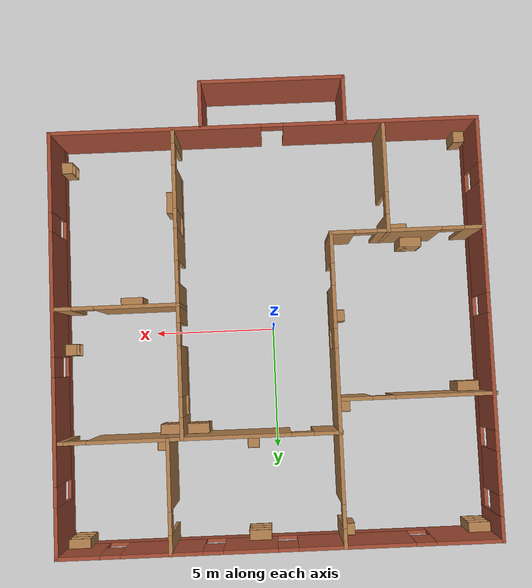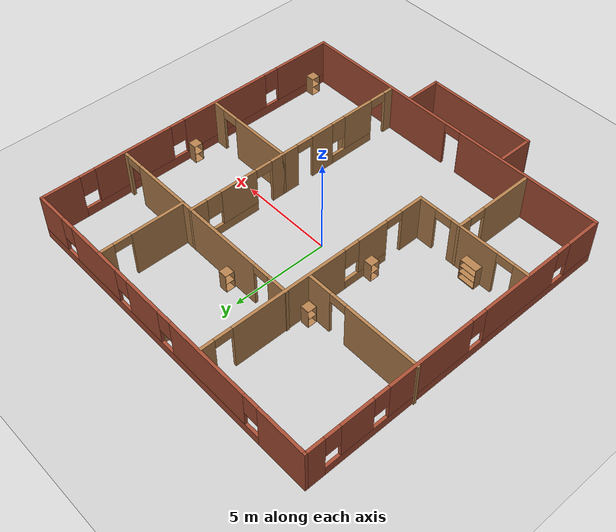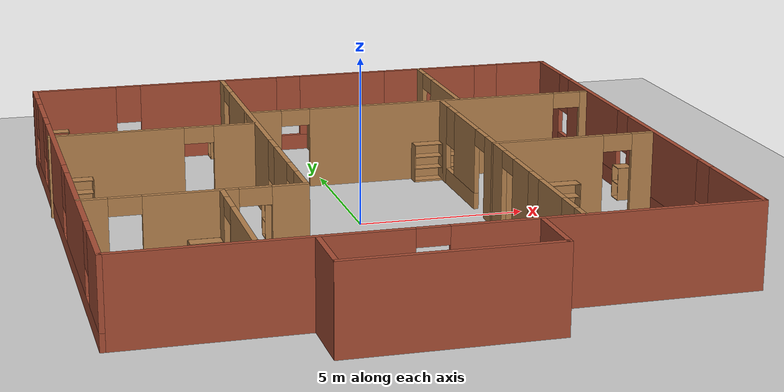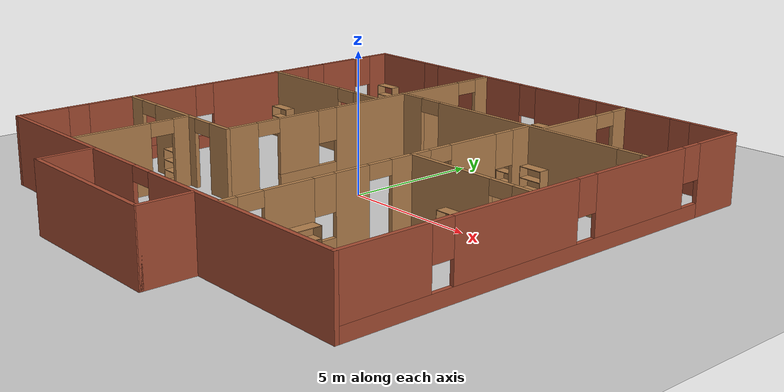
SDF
<sdf version="1.7">
 <world name="default">
  <light name="sun" type="directional">
   <pose>0 0 10 0 -0 0</pose>
   <diffuse>0.8 0.8 0.8 1</diffuse>
   <specular>0.2 0.2 0.2 1</specular>
   <attenuation>
    <range>1000</range>
    <constant>0.9</constant>
    <linear>0.01</linear>
    <quadratic>0.001</quadratic>
   </attenuation>
   <direction>-0.5 0.1 -0.9</direction>
   <spot><inner_angle>0</inner_angle><outer_angle>0</outer_angle><falloff>0</falloff></spot>
  </light>
  <model name="ground_plane">
   <static>1</static>
   <link name="link">
    <collision name="collision">
     <geometry><plane><normal>0 0 1</normal><size>100 100</size></plane></geometry>
     <surface>
      <contact><collide_bitmask>65535</collide_bitmask></contact>
      <friction><ode><mu>100</mu><mu2>50</mu2></ode></friction>
     </surface>
    </collision>
    <visual name="visual">
     <cast_shadows>0</cast_shadows>
     <geometry><plane><normal>0 0 1</normal><size>100 100</size></plane></geometry>
     <material>
      <script><uri>file://media/materials/scripts/gazebo.material</uri><name>Gazebo/Grey</name></script>
     </material>
    </visual>
   </link>
  </model>
  <gravity>0 0 -9.8</gravity>
  <magnetic_field>6e-06 2.3e-05 -4.2e-05</magnetic_field>
  <atmosphere type="adiabatic"/>
  <physics type="ode">
   <max_step_size>0.001</max_step_size>
   <real_time_factor>1</real_time_factor>
   <real_time_update_rate>1000</real_time_update_rate>
  </physics>
  <scene><ambient>0.4 0.4 0.4 1</ambient><background>0.7 0.7 0.7 1</background><shadows>1</shadows></scene>
  <audio><device>default</device></audio>
  <spherical_coordinates>
   <surface_model>EARTH_WGS84</surface_model>
   <latitude_deg>0</latitude_deg>
   <longitude_deg>0</longitude_deg>
   <elevation>0</elevation>
   <heading_deg>0</heading_deg>
  </spherical_coordinates>
  <model name="floor_world">
   <pose>0.06506 -0.674263 0 0 -0 0</pose>
   <link name="Wall_10">
    <collision name="Wall_10_Collision">
     <geometry><box><size>2 0.15 2.5</size></box></geometry>
     <pose>0 0 1.25 0 -0 0</pose>
    </collision>
    <visual name="Wall_10_Visual">
     <pose>0 0 1.25 0 -0 0</pose>
     <geometry><box><size>2 0.15 2.5</size></box></geometry>
     <material>
      <script><uri>file://media/materials/scripts/gazebo.material</uri><name>Gazebo/Bricks</name></script>
      <ambient>1 1 1 1</ambient>
     </material>
     <meta><layer>0</layer></meta>
    </visual>
    <pose>-3.28762 -8.41095 0 0 -0 -1.5708</pose>
   </link>
   <link name="Wall_11">
    <collision name="Wall_11_Collision">
     <geometry><box><size>6 0.15 2.5</size></box></geometry>
     <pose>0 0 1.25 0 -0 0</pose>
    </collision>
    <visual name="Wall_11_Visual">
     <pose>0 0 1.25 0 -0 0</pose>
     <geometry><box><size>6 0.15 2.5</size></box></geometry>
     <material>
      <script><uri>file://media/materials/scripts/gazebo.material</uri><name>Gazebo/Bricks</name></script>
      <ambient>1 1 1 1</ambient>
     </material>
     <meta><layer>0</layer></meta>
    </visual>
    <pose>-0.362616 -9.37641 0 0 -0 0</pose>
   </link>
   <link name="Wall_12">
    <collision name="Wall_12_Collision">
     <geometry><box><size>1.89729 0.15 2.5</size></box></geometry>
     <pose>0 0 1.25 0 -0 0</pose>
    </collision>
    <visual name="Wall_12_Visual">
     <pose>0 0 1.25 0 -0 0</pose>
     <geometry><box><size>1.89729 0.15 2.5</size></box></geometry>
     <material>
      <script><uri>file://media/materials/scripts/gazebo.material</uri><name>Gazebo/Bricks</name></script>
      <ambient>1 1 1 1</ambient>
     </material>
     <meta><layer>0</layer></meta>
    </visual>
    <pose>2.56238 -8.46231 0 0 -0 1.5708</pose>
   </link>
   <link name="Wall_14">
    <pose>-2.51896 3.19449 0 0 -0 -1.5708</pose>
    <visual name="Wall_14_Visual_0">
     <pose>-5.85089 0 1.25 0 -0 0</pose>
     <geometry><box><size>0.798212 0.15 2.5</size></box></geometry>
     <material>
      <script><uri>file://media/materials/scripts/gazebo.material</uri><name>Gazebo/Wood</name></script>
      <ambient>1 1 1 1</ambient>
     </material>
     <meta><layer>0</layer></meta>
    </visual>
    <collision name="Wall_14_Collision_0">
     <geometry><box><size>0.798212 0.15 2.5</size></box></geometry>
     <pose>-5.85089 0 1.25 0 -0 0</pose>
    </collision>
    <visual name="Wall_14_Visual_1">
     <pose>-1.50357 0 1.25 0 -0 0</pose>
     <geometry><box><size>6.09644 0.15 2.5</size></box></geometry>
     <material>
      <script><uri>file://media/materials/scripts/gazebo.material</uri><name>Gazebo/Wood</name></script>
      <ambient>1 1 1 1</ambient>
     </material>
     <meta><layer>0</layer></meta>
    </visual>
    <collision name="Wall_14_Collision_1">
     <geometry><box><size>6.09644 0.15 2.5</size></box></geometry>
     <pose>-1.50357 0 1.25 0 -0 0</pose>
    </collision>
    <visual name="Wall_14_Visual_2">
     <pose>5.5981 0 1.25 0 -0 0</pose>
     <geometry><box><size>1.3038 0.15 2.5</size></box></geometry>
     <material>
      <script><uri>file://media/materials/scripts/gazebo.material</uri><name>Gazebo/Wood</name></script>
      <ambient>1 1 1 1</ambient>
     </material>
     <meta><layer>0</layer></meta>
    </visual>
    <collision name="Wall_14_Collision_2">
     <geometry><box><size>1.3038 0.15 2.5</size></box></geometry>
     <pose>5.5981 0 1.25 0 -0 0</pose>
    </collision>
    <visual name="Wall_14_Visual_3">
     <pose>2.79542 0 0.25 0 -0 0</pose>
     <geometry><box><size>2.50155 0.15 0.5</size></box></geometry>
     <material>
      <script><uri>file://media/materials/scripts/gazebo.material</uri><name>Gazebo/Wood</name></script>
      <ambient>1 1 1 1</ambient>
     </material>
     <meta><layer>0</layer></meta>
    </visual>
    <collision name="Wall_14_Collision_3">
     <geometry><box><size>2.50155 0.15 0.5</size></box></geometry>
     <pose>2.79542 0 0.25 0 -0 0</pose>
    </collision>
    <visual name="Wall_14_Visual_4">
     <pose>3.19543 0 1.5 0 -0 0</pose>
     <geometry><box><size>1.70155 0.15 2</size></box></geometry>
     <material>
      <script><uri>file://media/materials/scripts/gazebo.material</uri><name>Gazebo/Wood</name></script>
      <ambient>1 1 1 1</ambient>
     </material>
     <meta><layer>0</layer></meta>
    </visual>
    <collision name="Wall_14_Collision_4">
     <geometry><box><size>1.70155 0.15 2</size></box></geometry>
     <pose>3.19543 0 1.5 0 -0 0</pose>
    </collision>
    <visual name="Wall_14_Visual_5">
     <pose>1.94465 0 1.9 0 -0 0</pose>
     <geometry><box><size>0.8 0.15 1.2</size></box></geometry>
     <material>
      <script><uri>file://media/materials/scripts/gazebo.material</uri><name>Gazebo/Wood</name></script>
      <ambient>1 1 1 1</ambient>
     </material>
     <meta><layer>0</layer></meta>
    </visual>
    <collision name="Wall_14_Collision_5">
     <geometry><box><size>0.8 0.15 1.2</size></box></geometry>
     <pose>1.94465 0 1.9 0 -0 0</pose>
    </collision>
    <visual name="Wall_14_Visual_6">
     <pose>-5.00179 0 2.25 0 -0 0</pose>
     <geometry><box><size>0.9 0.15 0.5</size></box></geometry>
     <material>
      <script><uri>file://media/materials/scripts/gazebo.material</uri><name>Gazebo/Wood</name></script>
      <ambient>1 1 1 1</ambient>
     </material>
     <meta><layer>0</layer></meta>
    </visual>
    <collision name="Wall_14_Collision_6">
     <geometry><box><size>0.9 0.15 0.5</size></box></geometry>
     <pose>-5.00179 0 2.25 0 -0 0</pose>
    </collision>
    <visual name="Wall_14_Visual_7">
     <pose>4.4962 0 2.25 0 -0 0</pose>
     <geometry><box><size>0.9 0.15 0.5</size></box></geometry>
     <material>
      <script><uri>file://media/materials/scripts/gazebo.material</uri><name>Gazebo/Wood</name></script>
      <ambient>1 1 1 1</ambient>
     </material>
     <meta><layer>0</layer></meta>
    </visual>
    <collision name="Wall_14_Collision_7">
     <geometry><box><size>0.9 0.15 0.5</size></box></geometry>
     <pose>4.4962 0 2.25 0 -0 0</pose>
    </collision>
   </link>
   <link name="Wall_15">
    <pose>-5.56896 -2.98051 0 0 -0 3.14159</pose>
    <visual name="Wall_15_Visual_0">
     <pose>-2.61101 0 1.25 0 -0 0</pose>
     <geometry><box><size>1.02798 0.15 2.5</size></box></geometry>
     <material>
      <script><uri>file://media/materials/scripts/gazebo.material</uri><name>Gazebo/Wood</name></script>
      <ambient>1 1 1 1</ambient>
     </material>
     <meta><layer>0</layer></meta>
    </visual>
    <collision name="Wall_15_Collision_0">
     <geometry><box><size>1.02798 0.15 2.5</size></box></geometry>
     <pose>-2.61101 0 1.25 0 -0 0</pose>
    </collision>
    <visual name="Wall_15_Visual_1">
     <pose>0.099053 0 1.25 0 -0 0</pose>
     <geometry><box><size>2.59214 0.15 2.5</size></box></geometry>
     <material>
      <script><uri>file://media/materials/scripts/gazebo.material</uri><name>Gazebo/Wood</name></script>
      <ambient>1 1 1 1</ambient>
     </material>
     <meta><layer>0</layer></meta>
    </visual>
    <collision name="Wall_15_Collision_1">
     <geometry><box><size>2.59214 0.15 2.5</size></box></geometry>
     <pose>0.099053 0 1.25 0 -0 0</pose>
    </collision>
    <visual name="Wall_15_Visual_2">
     <pose>2.71006 0 1.25 0 -0 0</pose>
     <geometry><box><size>0.829875 0.15 2.5</size></box></geometry>
     <material>
      <script><uri>file://media/materials/scripts/gazebo.material</uri><name>Gazebo/Wood</name></script>
      <ambient>1 1 1 1</ambient>
     </material>
     <meta><layer>0</layer></meta>
    </visual>
    <collision name="Wall_15_Collision_2">
     <geometry><box><size>0.829875 0.15 2.5</size></box></geometry>
     <pose>2.71006 0 1.25 0 -0 0</pose>
    </collision>
    <visual name="Wall_15_Visual_3">
     <pose>-1.64702 0 2.25 0 -0 0</pose>
     <geometry><box><size>0.9 0.15 0.5</size></box></geometry>
     <material>
      <script><uri>file://media/materials/scripts/gazebo.material</uri><name>Gazebo/Wood</name></script>
      <ambient>1 1 1 1</ambient>
     </material>
     <meta><layer>0</layer></meta>
    </visual>
    <collision name="Wall_15_Collision_3">
     <geometry><box><size>0.9 0.15 0.5</size></box></geometry>
     <pose>-1.64702 0 2.25 0 -0 0</pose>
    </collision>
    <visual name="Wall_15_Visual_4">
     <pose>1.84512 0 2.25 0 -0 0</pose>
     <geometry><box><size>0.9 0.15 0.5</size></box></geometry>
     <material>
      <script><uri>file://media/materials/scripts/gazebo.material</uri><name>Gazebo/Wood</name></script>
      <ambient>1 1 1 1</ambient>
     </material>
     <meta><layer>0</layer></meta>
    </visual>
    <collision name="Wall_15_Collision_4">
     <geometry><box><size>0.9 0.15 0.5</size></box></geometry>
     <pose>1.84512 0 2.25 0 -0 0</pose>
    </collision>
   </link>
   <link name="Wall_17">
    <pose>2.99058 4.95983 0 0 -0 0</pose>
    <visual name="Wall_17_Visual_0">
     <pose>-5.05152 0 1.25 0 -0 0</pose>
     <geometry><box><size>1.14696 0.15 2.5</size></box></geometry>
     <material>
      <script><uri>file://media/materials/scripts/gazebo.material</uri><name>Gazebo/Wood</name></script>
      <ambient>1 1 1 1</ambient>
     </material>
     <meta><layer>0</layer></meta>
    </visual>
    <collision name="Wall_17_Collision_0">
     <geometry><box><size>1.14696 0.15 2.5</size></box></geometry>
     <pose>-5.05152 0 1.25 0 -0 0</pose>
    </collision>
    <visual name="Wall_17_Visual_1">
     <pose>0.449976 0 1.25 0 -0 0</pose>
     <geometry><box><size>8.05604 0.15 2.5</size></box></geometry>
     <material>
      <script><uri>file://media/materials/scripts/gazebo.material</uri><name>Gazebo/Wood</name></script>
      <ambient>1 1 1 1</ambient>
     </material>
     <meta><layer>0</layer></meta>
    </visual>
    <collision name="Wall_17_Collision_1">
     <geometry><box><size>8.05604 0.15 2.5</size></box></geometry>
     <pose>0.449976 0 1.25 0 -0 0</pose>
    </collision>
    <visual name="Wall_17_Visual_2">
     <pose>5.5015 0 1.25 0 -0 0</pose>
     <geometry><box><size>0.247005 0.15 2.5</size></box></geometry>
     <material>
      <script><uri>file://media/materials/scripts/gazebo.material</uri><name>Gazebo/Wood</name></script>
      <ambient>1 1 1 1</ambient>
     </material>
     <meta><layer>0</layer></meta>
    </visual>
    <collision name="Wall_17_Collision_2">
     <geometry><box><size>0.247005 0.15 2.5</size></box></geometry>
     <pose>5.5015 0 1.25 0 -0 0</pose>
    </collision>
    <visual name="Wall_17_Visual_3">
     <pose>-4.02804 0 2.25 0 -0 0</pose>
     <geometry><box><size>0.9 0.15 0.5</size></box></geometry>
     <material>
      <script><uri>file://media/materials/scripts/gazebo.material</uri><name>Gazebo/Wood</name></script>
      <ambient>1 1 1 1</ambient>
     </material>
     <meta><layer>0</layer></meta>
    </visual>
    <collision name="Wall_17_Collision_3">
     <geometry><box><size>0.9 0.15 0.5</size></box></geometry>
     <pose>-4.02804 0 2.25 0 -0 0</pose>
    </collision>
    <visual name="Wall_17_Visual_4">
     <pose>4.928 0 2.25 0 -0 0</pose>
     <geometry><box><size>0.9 0.15 0.5</size></box></geometry>
     <material>
      <script><uri>file://media/materials/scripts/gazebo.material</uri><name>Gazebo/Wood</name></script>
      <ambient>1 1 1 1</ambient>
     </material>
     <meta><layer>0</layer></meta>
    </visual>
    <collision name="Wall_17_Collision_4">
     <geometry><box><size>0.9 0.15 0.5</size></box></geometry>
     <pose>4.928 0 2.25 0 -0 0</pose>
    </collision>
   </link>
   <link name="Wall_19">
    <pose>3.7112 -1.21517 0 0 -0 -1.5708</pose>
    <visual name="Wall_19_Visual_0">
     <pose>-5.79039 0 1.25 0 -0 0</pose>
     <geometry><box><size>0.919224 0.15 2.5</size></box></geometry>
     <material>
      <script><uri>file://media/materials/scripts/gazebo.material</uri><name>Gazebo/Wood</name></script>
      <ambient>1 1 1 1</ambient>
     </material>
     <meta><layer>0</layer></meta>
    </visual>
    <collision name="Wall_19_Collision_0">
     <geometry><box><size>0.919224 0.15 2.5</size></box></geometry>
     <pose>-5.79039 0 1.25 0 -0 0</pose>
    </collision>
    <visual name="Wall_19_Visual_1">
     <pose>-0.794408 0 1.25 0 -0 0</pose>
     <geometry><box><size>1.60825 0.15 2.5</size></box></geometry>
     <material>
      <script><uri>file://media/materials/scripts/gazebo.material</uri><name>Gazebo/Wood</name></script>
      <ambient>1 1 1 1</ambient>
     </material>
     <meta><layer>0</layer></meta>
    </visual>
    <collision name="Wall_19_Collision_1">
     <geometry><box><size>1.60825 0.15 2.5</size></box></geometry>
     <pose>-0.794408 0 1.25 0 -0 0</pose>
    </collision>
    <visual name="Wall_19_Visual_2">
     <pose>1.55791 0 1.25 0 -0 0</pose>
     <geometry><box><size>1.29638 0.15 2.5</size></box></geometry>
     <material>
      <script><uri>file://media/materials/scripts/gazebo.material</uri><name>Gazebo/Wood</name></script>
      <ambient>1 1 1 1</ambient>
     </material>
     <meta><layer>0</layer></meta>
    </visual>
    <collision name="Wall_19_Collision_2">
     <geometry><box><size>1.29638 0.15 2.5</size></box></geometry>
     <pose>1.55791 0 1.25 0 -0 0</pose>
    </collision>
    <visual name="Wall_19_Visual_3">
     <pose>5.96674 0 1.25 0 -0 0</pose>
     <geometry><box><size>0.566527 0.15 2.5</size></box></geometry>
     <material>
      <script><uri>file://media/materials/scripts/gazebo.material</uri><name>Gazebo/Wood</name></script>
      <ambient>1 1 1 1</ambient>
     </material>
     <meta><layer>0</layer></meta>
    </visual>
    <collision name="Wall_19_Collision_3">
     <geometry><box><size>0.566527 0.15 2.5</size></box></geometry>
     <pose>5.96674 0 1.25 0 -0 0</pose>
    </collision>
    <visual name="Wall_19_Visual_4">
     <pose>-3.91465 0 0.25 0 -0 0</pose>
     <geometry><box><size>2.83224 0.15 0.5</size></box></geometry>
     <material>
      <script><uri>file://media/materials/scripts/gazebo.material</uri><name>Gazebo/Wood</name></script>
      <ambient>1 1 1 1</ambient>
     </material>
     <meta><layer>0</layer></meta>
    </visual>
    <collision name="Wall_19_Collision_4">
     <geometry><box><size>2.83224 0.15 0.5</size></box></geometry>
     <pose>-3.91465 0 0.25 0 -0 0</pose>
    </collision>
    <visual name="Wall_19_Visual_5">
     <pose>3.49478 0 0.25 0 -0 0</pose>
     <geometry><box><size>2.57737 0.15 0.5</size></box></geometry>
     <material>
      <script><uri>file://media/materials/scripts/gazebo.material</uri><name>Gazebo/Wood</name></script>
      <ambient>1 1 1 1</ambient>
     </material>
     <meta><layer>0</layer></meta>
    </visual>
    <collision name="Wall_19_Collision_5">
     <geometry><box><size>2.57737 0.15 0.5</size></box></geometry>
     <pose>3.49478 0 0.25 0 -0 0</pose>
    </collision>
    <visual name="Wall_19_Visual_6">
     <pose>-3.51465 0 1.5 0 -0 0</pose>
     <geometry><box><size>2.03224 0.15 2</size></box></geometry>
     <material>
      <script><uri>file://media/materials/scripts/gazebo.material</uri><name>Gazebo/Wood</name></script>
      <ambient>1 1 1 1</ambient>
     </material>
     <meta><layer>0</layer></meta>
    </visual>
    <collision name="Wall_19_Collision_6">
     <geometry><box><size>2.03224 0.15 2</size></box></geometry>
     <pose>-3.51465 0 1.5 0 -0 0</pose>
    </collision>
    <visual name="Wall_19_Visual_7">
     <pose>-3.51465 0 1.5 0 -0 0</pose>
     <geometry><box><size>2.03224 0.15 2</size></box></geometry>
     <material>
      <script><uri>file://media/materials/scripts/gazebo.material</uri><name>Gazebo/Wood</name></script>
      <ambient>1 1 1 1</ambient>
     </material>
     <meta><layer>0</layer></meta>
    </visual>
    <collision name="Wall_19_Collision_7">
     <geometry><box><size>2.03224 0.15 2</size></box></geometry>
     <pose>-3.51465 0 1.5 0 -0 0</pose>
    </collision>
    <visual name="Wall_19_Visual_8">
     <pose>3.89479 0 1.5 0 -0 0</pose>
     <geometry><box><size>1.77737 0.15 2</size></box></geometry>
     <material>
      <script><uri>file://media/materials/scripts/gazebo.material</uri><name>Gazebo/Wood</name></script>
      <ambient>1 1 1 1</ambient>
     </material>
     <meta><layer>0</layer></meta>
    </visual>
    <collision name="Wall_19_Collision_8">
     <geometry><box><size>1.77737 0.15 2</size></box></geometry>
     <pose>3.89479 0 1.5 0 -0 0</pose>
    </collision>
    <visual name="Wall_19_Visual_9">
     <pose>-4.93078 0 1.9 0 -0 0</pose>
     <geometry><box><size>0.8 0.15 1.2</size></box></geometry>
     <material>
      <script><uri>file://media/materials/scripts/gazebo.material</uri><name>Gazebo/Wood</name></script>
      <ambient>1 1 1 1</ambient>
     </material>
     <meta><layer>0</layer></meta>
    </visual>
    <collision name="Wall_19_Collision_9">
     <geometry><box><size>0.8 0.15 1.2</size></box></geometry>
     <pose>-4.93078 0 1.9 0 -0 0</pose>
    </collision>
    <visual name="Wall_19_Visual_10">
     <pose>2.6061 0 1.9 0 -0 0</pose>
     <geometry><box><size>0.8 0.15 1.2</size></box></geometry>
     <material>
      <script><uri>file://media/materials/scripts/gazebo.material</uri><name>Gazebo/Wood</name></script>
      <ambient>1 1 1 1</ambient>
     </material>
     <meta><layer>0</layer></meta>
    </visual>
    <collision name="Wall_19_Collision_10">
     <geometry><box><size>0.8 0.15 1.2</size></box></geometry>
     <pose>2.6061 0 1.9 0 -0 0</pose>
    </collision>
    <visual name="Wall_19_Visual_11">
     <pose>0.459715 0 2.25 0 -0 0</pose>
     <geometry><box><size>0.9 0.15 0.5</size></box></geometry>
     <material>
      <script><uri>file://media/materials/scripts/gazebo.material</uri><name>Gazebo/Wood</name></script>
      <ambient>1 1 1 1</ambient>
     </material>
     <meta><layer>0</layer></meta>
    </visual>
    <collision name="Wall_19_Collision_11">
     <geometry><box><size>0.9 0.15 0.5</size></box></geometry>
     <pose>0.459715 0 2.25 0 -0 0</pose>
    </collision>
    <visual name="Wall_19_Visual_12">
     <pose>-2.04853 0 2.25 0 -0 0</pose>
     <geometry><box><size>0.9 0.15 0.5</size></box></geometry>
     <material>
      <script><uri>file://media/materials/scripts/gazebo.material</uri><name>Gazebo/Wood</name></script>
      <ambient>1 1 1 1</ambient>
     </material>
     <meta><layer>0</layer></meta>
    </visual>
    <collision name="Wall_19_Collision_12">
     <geometry><box><size>0.9 0.15 0.5</size></box></geometry>
     <pose>-2.04853 0 2.25 0 -0 0</pose>
    </collision>
    <visual name="Wall_19_Visual_13">
     <pose>-2.04853 0 2.25 0 -0 0</pose>
     <geometry><box><size>0.9 0.15 0.5</size></box></geometry>
     <material>
      <script><uri>file://media/materials/scripts/gazebo.material</uri><name>Gazebo/Wood</name></script>
      <ambient>1 1 1 1</ambient>
     </material>
     <meta><layer>0</layer></meta>
    </visual>
    <collision name="Wall_19_Collision_13">
     <geometry><box><size>0.9 0.15 0.5</size></box></geometry>
     <pose>-2.04853 0 2.25 0 -0 0</pose>
    </collision>
    <visual name="Wall_19_Visual_14">
     <pose>5.23347 0 2.25 0 -0 0</pose>
     <geometry><box><size>0.9 0.15 0.5</size></box></geometry>
     <material>
      <script><uri>file://media/materials/scripts/gazebo.material</uri><name>Gazebo/Wood</name></script>
      <ambient>1 1 1 1</ambient>
     </material>
     <meta><layer>0</layer></meta>
    </visual>
    <collision name="Wall_19_Collision_14">
     <geometry><box><size>0.9 0.15 0.5</size></box></geometry>
     <pose>5.23347 0 2.25 0 -0 0</pose>
    </collision>
   </link>
   <link name="Wall_21">
    <pose>-4.82493 -5.14446 0 0 -0 -1.5708</pose>
    <visual name="Wall_21_Visual_0">
     <pose>-1.87203 0 1.25 0 -0 0</pose>
     <geometry><box><size>0.755949 0.15 2.5</size></box></geometry>
     <material>
      <script><uri>file://media/materials/scripts/gazebo.material</uri><name>Gazebo/Wood</name></script>
      <ambient>1 1 1 1</ambient>
     </material>
     <meta><layer>0</layer></meta>
    </visual>
    <collision name="Wall_21_Collision_0">
     <geometry><box><size>0.755949 0.15 2.5</size></box></geometry>
     <pose>-1.87203 0 1.25 0 -0 0</pose>
    </collision>
    <visual name="Wall_21_Visual_1">
     <pose>0.827974 0 1.25 0 -0 0</pose>
     <geometry><box><size>2.84405 0.15 2.5</size></box></geometry>
     <material>
      <script><uri>file://media/materials/scripts/gazebo.material</uri><name>Gazebo/Wood</name></script>
      <ambient>1 1 1 1</ambient>
     </material>
     <meta><layer>0</layer></meta>
    </visual>
    <collision name="Wall_21_Collision_1">
     <geometry><box><size>2.84405 0.15 2.5</size></box></geometry>
     <pose>0.827974 0 1.25 0 -0 0</pose>
    </collision>
    <visual name="Wall_21_Visual_2">
     <pose>-1.04405 0 2.25 0 -0 0</pose>
     <geometry><box><size>0.9 0.15 0.5</size></box></geometry>
     <material>
      <script><uri>file://media/materials/scripts/gazebo.material</uri><name>Gazebo/Wood</name></script>
      <ambient>1 1 1 1</ambient>
     </material>
     <meta><layer>0</layer></meta>
    </visual>
    <collision name="Wall_21_Collision_2">
     <geometry><box><size>0.9 0.15 0.5</size></box></geometry>
     <pose>-1.04405 0 2.25 0 -0 0</pose>
    </collision>
   </link>
   <link name="Wall_23">
    <pose>-5.65866 3.66526 0 0 -0 0</pose>
    <visual name="Wall_23_Visual_0">
     <pose>-1.10767 0 1.25 0 -0 0</pose>
     <geometry><box><size>4.03466 0.15 2.5</size></box></geometry>
     <material>
      <script><uri>file://media/materials/scripts/gazebo.material</uri><name>Gazebo/Wood</name></script>
      <ambient>1 1 1 1</ambient>
     </material>
     <meta><layer>0</layer></meta>
    </visual>
    <collision name="Wall_23_Collision_0">
     <geometry><box><size>4.03466 0.15 2.5</size></box></geometry>
     <pose>-1.10767 0 1.25 0 -0 0</pose>
    </collision>
    <visual name="Wall_23_Visual_1">
     <pose>2.46733 0 1.25 0 -0 0</pose>
     <geometry><box><size>1.31534 0.15 2.5</size></box></geometry>
     <material>
      <script><uri>file://media/materials/scripts/gazebo.material</uri><name>Gazebo/Wood</name></script>
      <ambient>1 1 1 1</ambient>
     </material>
     <meta><layer>0</layer></meta>
    </visual>
    <collision name="Wall_23_Collision_1">
     <geometry><box><size>1.31534 0.15 2.5</size></box></geometry>
     <pose>2.46733 0 1.25 0 -0 0</pose>
    </collision>
    <visual name="Wall_23_Visual_2">
     <pose>1.35966 0 2.25 0 -0 0</pose>
     <geometry><box><size>0.9 0.15 0.5</size></box></geometry>
     <material>
      <script><uri>file://media/materials/scripts/gazebo.material</uri><name>Gazebo/Wood</name></script>
      <ambient>1 1 1 1</ambient>
     </material>
     <meta><layer>0</layer></meta>
    </visual>
    <collision name="Wall_23_Collision_2">
     <geometry><box><size>0.9 0.15 0.5</size></box></geometry>
     <pose>1.35966 0 2.25 0 -0 0</pose>
    </collision>
   </link>
   <link name="Wall_25">
    <pose>6.1362 -0.339847 0 0 -0 0</pose>
    <visual name="Wall_25_Visual_0">
     <pose>-0.786088 0 1.25 0 -0 0</pose>
     <geometry><box><size>3.42782 0.15 2.5</size></box></geometry>
     <material>
      <script><uri>file://media/materials/scripts/gazebo.material</uri><name>Gazebo/Wood</name></script>
      <ambient>1 1 1 1</ambient>
     </material>
     <meta><layer>0</layer></meta>
    </visual>
    <collision name="Wall_25_Collision_0">
     <geometry><box><size>3.42782 0.15 2.5</size></box></geometry>
     <pose>-0.786088 0 1.25 0 -0 0</pose>
    </collision>
    <visual name="Wall_25_Visual_1">
     <pose>2.16391 0 1.25 0 -0 0</pose>
     <geometry><box><size>0.672176 0.15 2.5</size></box></geometry>
     <material>
      <script><uri>file://media/materials/scripts/gazebo.material</uri><name>Gazebo/Wood</name></script>
      <ambient>1 1 1 1</ambient>
     </material>
     <meta><layer>0</layer></meta>
    </visual>
    <collision name="Wall_25_Collision_1">
     <geometry><box><size>0.672176 0.15 2.5</size></box></geometry>
     <pose>2.16391 0 1.25 0 -0 0</pose>
    </collision>
    <visual name="Wall_25_Visual_2">
     <pose>1.37782 0 2.25 0 -0 0</pose>
     <geometry><box><size>0.9 0.15 0.5</size></box></geometry>
     <material>
      <script><uri>file://media/materials/scripts/gazebo.material</uri><name>Gazebo/Wood</name></script>
      <ambient>1 1 1 1</ambient>
     </material>
     <meta><layer>0</layer></meta>
    </visual>
    <collision name="Wall_25_Collision_2">
     <geometry><box><size>0.9 0.15 0.5</size></box></geometry>
     <pose>1.37782 0 2.25 0 -0 0</pose>
    </collision>
   </link>
   <link name="Wall_27">
    <pose>4.27758 7.15404 0 0 -0 -1.5708</pose>
    <visual name="Wall_27_Visual_0">
     <pose>-1.87112 0 1.25 0 -0 0</pose>
     <geometry><box><size>0.757756 0.15 2.5</size></box></geometry>
     <material>
      <script><uri>file://media/materials/scripts/gazebo.material</uri><name>Gazebo/Wood</name></script>
      <ambient>1 1 1 1</ambient>
     </material>
     <meta><layer>0</layer></meta>
    </visual>
    <collision name="Wall_27_Collision_0">
     <geometry><box><size>0.757756 0.15 2.5</size></box></geometry>
     <pose>-1.87112 0 1.25 0 -0 0</pose>
    </collision>
    <visual name="Wall_27_Visual_1">
     <pose>0.828878 0 1.25 0 -0 0</pose>
     <geometry><box><size>2.84224 0.15 2.5</size></box></geometry>
     <material>
      <script><uri>file://media/materials/scripts/gazebo.material</uri><name>Gazebo/Wood</name></script>
      <ambient>1 1 1 1</ambient>
     </material>
     <meta><layer>0</layer></meta>
    </visual>
    <collision name="Wall_27_Collision_1">
     <geometry><box><size>2.84224 0.15 2.5</size></box></geometry>
     <pose>0.828878 0 1.25 0 -0 0</pose>
    </collision>
    <visual name="Wall_27_Visual_2">
     <pose>-1.04224 0 2.25 0 -0 0</pose>
     <geometry><box><size>0.9 0.15 0.5</size></box></geometry>
     <material>
      <script><uri>file://media/materials/scripts/gazebo.material</uri><name>Gazebo/Wood</name></script>
      <ambient>1 1 1 1</ambient>
     </material>
     <meta><layer>0</layer></meta>
    </visual>
    <collision name="Wall_27_Collision_2">
     <geometry><box><size>0.9 0.15 0.5</size></box></geometry>
     <pose>-1.04224 0 2.25 0 -0 0</pose>
    </collision>
   </link>
   <link name="Wall_4">
    <pose>-8.64134 0.951405 0 0 -0 -1.5708</pose>
    <visual name="Wall_4_Visual_0">
     <pose>-7.99546 0 1.25 0 -0 0</pose>
     <geometry><box><size>1.00907 0.15 2.5</size></box></geometry>
     <material>
      <script><uri>file://media/materials/scripts/gazebo.material</uri><name>Gazebo/Bricks</name></script>
      <ambient>1 1 1 1</ambient>
     </material>
     <meta><layer>0</layer></meta>
    </visual>
    <collision name="Wall_4_Collision_0">
     <geometry><box><size>1.00907 0.15 2.5</size></box></geometry>
     <pose>-7.99546 0 1.25 0 -0 0</pose>
    </collision>
    <visual name="Wall_4_Visual_1">
     <pose>0.504536 0 0.25 0 -0 0</pose>
     <geometry><box><size>15.9909 0.15 0.5</size></box></geometry>
     <material>
      <script><uri>file://media/materials/scripts/gazebo.material</uri><name>Gazebo/Bricks</name></script>
      <ambient>1 1 1 1</ambient>
     </material>
     <meta><layer>0</layer></meta>
    </visual>
    <collision name="Wall_4_Collision_1">
     <geometry><box><size>15.9909 0.15 0.5</size></box></geometry>
     <pose>0.504536 0 0.25 0 -0 0</pose>
    </collision>
    <visual name="Wall_4_Visual_2">
     <pose>-5.83478 0 1.5 0 -0 0</pose>
     <geometry><box><size>1.71229 0.15 2</size></box></geometry>
     <material>
      <script><uri>file://media/materials/scripts/gazebo.material</uri><name>Gazebo/Bricks</name></script>
      <ambient>1 1 1 1</ambient>
     </material>
     <meta><layer>0</layer></meta>
    </visual>
    <collision name="Wall_4_Collision_2">
     <geometry><box><size>1.71229 0.15 2</size></box></geometry>
     <pose>-5.83478 0 1.5 0 -0 0</pose>
    </collision>
    <visual name="Wall_4_Visual_3">
     <pose>-1.85699 0 1.5 0 -0 0</pose>
     <geometry><box><size>4.6433 0.15 2</size></box></geometry>
     <material>
      <script><uri>file://media/materials/scripts/gazebo.material</uri><name>Gazebo/Bricks</name></script>
      <ambient>1 1 1 1</ambient>
     </material>
     <meta><layer>0</layer></meta>
    </visual>
    <collision name="Wall_4_Collision_3">
     <geometry><box><size>4.6433 0.15 2</size></box></geometry>
     <pose>-1.85699 0 1.5 0 -0 0</pose>
    </collision>
    <visual name="Wall_4_Visual_4">
     <pose>3.51652 0 1.5 0 -0 0</pose>
     <geometry><box><size>4.50373 0.15 2</size></box></geometry>
     <material>
      <script><uri>file://media/materials/scripts/gazebo.material</uri><name>Gazebo/Bricks</name></script>
      <ambient>1 1 1 1</ambient>
     </material>
     <meta><layer>0</layer></meta>
    </visual>
    <collision name="Wall_4_Collision_4">
     <geometry><box><size>4.50373 0.15 2</size></box></geometry>
     <pose>3.51652 0 1.5 0 -0 0</pose>
    </collision>
    <visual name="Wall_4_Visual_5">
     <pose>7.53419 0 1.5 0 -0 0</pose>
     <geometry><box><size>1.93161 0.15 2</size></box></geometry>
     <material>
      <script><uri>file://media/materials/scripts/gazebo.material</uri><name>Gazebo/Bricks</name></script>
      <ambient>1 1 1 1</ambient>
     </material>
     <meta><layer>0</layer></meta>
    </visual>
    <collision name="Wall_4_Collision_5">
     <geometry><box><size>1.93161 0.15 2</size></box></geometry>
     <pose>7.53419 0 1.5 0 -0 0</pose>
    </collision>
    <visual name="Wall_4_Visual_6">
     <pose>-7.09093 0 1.9 0 -0 0</pose>
     <geometry><box><size>0.8 0.15 1.2</size></box></geometry>
     <material>
      <script><uri>file://media/materials/scripts/gazebo.material</uri><name>Gazebo/Bricks</name></script>
      <ambient>1 1 1 1</ambient>
     </material>
     <meta><layer>0</layer></meta>
    </visual>
    <collision name="Wall_4_Collision_6">
     <geometry><box><size>0.8 0.15 1.2</size></box></geometry>
     <pose>-7.09093 0 1.9 0 -0 0</pose>
    </collision>
    <visual name="Wall_4_Visual_7">
     <pose>-4.57864 0 1.9 0 -0 0</pose>
     <geometry><box><size>0.8 0.15 1.2</size></box></geometry>
     <material>
      <script><uri>file://media/materials/scripts/gazebo.material</uri><name>Gazebo/Bricks</name></script>
      <ambient>1 1 1 1</ambient>
     </material>
     <meta><layer>0</layer></meta>
    </visual>
    <collision name="Wall_4_Collision_7">
     <geometry><box><size>0.8 0.15 1.2</size></box></geometry>
     <pose>-4.57864 0 1.9 0 -0 0</pose>
    </collision>
    <visual name="Wall_4_Visual_8">
     <pose>0.864661 0 1.9 0 -0 0</pose>
     <geometry><box><size>0.8 0.15 1.2</size></box></geometry>
     <material>
      <script><uri>file://media/materials/scripts/gazebo.material</uri><name>Gazebo/Bricks</name></script>
      <ambient>1 1 1 1</ambient>
     </material>
     <meta><layer>0</layer></meta>
    </visual>
    <collision name="Wall_4_Collision_8">
     <geometry><box><size>0.8 0.15 1.2</size></box></geometry>
     <pose>0.864661 0 1.9 0 -0 0</pose>
    </collision>
    <visual name="Wall_4_Visual_9">
     <pose>6.16839 0 1.9 0 -0 0</pose>
     <geometry><box><size>0.8 0.15 1.2</size></box></geometry>
     <material>
      <script><uri>file://media/materials/scripts/gazebo.material</uri><name>Gazebo/Bricks</name></script>
      <ambient>1 1 1 1</ambient>
     </material>
     <meta><layer>0</layer></meta>
    </visual>
    <collision name="Wall_4_Collision_9">
     <geometry><box><size>0.8 0.15 1.2</size></box></geometry>
     <pose>6.16839 0 1.9 0 -0 0</pose>
    </collision>
   </link>
   <link name="Wall_6">
    <pose>0.033661 9.37641 0 0 -0 0</pose>
    <visual name="Wall_6_Visual_0">
     <pose>-7.41349 0 1.25 0 -0 0</pose>
     <geometry><box><size>2.67301 0.15 2.5</size></box></geometry>
     <material>
      <script><uri>file://media/materials/scripts/gazebo.material</uri><name>Gazebo/Bricks</name></script>
      <ambient>1 1 1 1</ambient>
     </material>
     <meta><layer>0</layer></meta>
    </visual>
    <collision name="Wall_6_Collision_0">
     <geometry><box><size>2.67301 0.15 2.5</size></box></geometry>
     <pose>-7.41349 0 1.25 0 -0 0</pose>
    </collision>
    <visual name="Wall_6_Visual_1">
     <pose>1.33651 0 0.25 0 -0 0</pose>
     <geometry><box><size>14.827 0.15 0.5</size></box></geometry>
     <material>
      <script><uri>file://media/materials/scripts/gazebo.material</uri><name>Gazebo/Bricks</name></script>
      <ambient>1 1 1 1</ambient>
     </material>
     <meta><layer>0</layer></meta>
    </visual>
    <collision name="Wall_6_Collision_1">
     <geometry><box><size>14.827 0.15 0.5</size></box></geometry>
     <pose>1.33651 0 0.25 0 -0 0</pose>
    </collision>
    <visual name="Wall_6_Visual_2">
     <pose>-3.00186 0 1.5 0 -0 0</pose>
     <geometry><box><size>4.55025 0.15 2</size></box></geometry>
     <material>
      <script><uri>file://media/materials/scripts/gazebo.material</uri><name>Gazebo/Bricks</name></script>
      <ambient>1 1 1 1</ambient>
     </material>
     <meta><layer>0</layer></meta>
    </visual>
    <collision name="Wall_6_Collision_2">
     <geometry><box><size>4.55025 0.15 2</size></box></geometry>
     <pose>-3.00186 0 1.5 0 -0 0</pose>
    </collision>
    <visual name="Wall_6_Visual_3">
     <pose>1.13877 0 1.5 0 -0 0</pose>
     <geometry><box><size>2.13101 0.15 2</size></box></geometry>
     <material>
      <script><uri>file://media/materials/scripts/gazebo.material</uri><name>Gazebo/Bricks</name></script>
      <ambient>1 1 1 1</ambient>
     </material>
     <meta><layer>0</layer></meta>
    </visual>
    <collision name="Wall_6_Collision_3">
     <geometry><box><size>2.13101 0.15 2</size></box></geometry>
     <pose>1.13877 0 1.5 0 -0 0</pose>
    </collision>
    <visual name="Wall_6_Visual_4">
     <pose>4.6048 0 1.5 0 -0 0</pose>
     <geometry><box><size>3.20106 0.15 2</size></box></geometry>
     <material>
      <script><uri>file://media/materials/scripts/gazebo.material</uri><name>Gazebo/Bricks</name></script>
      <ambient>1 1 1 1</ambient>
     </material>
     <meta><layer>0</layer></meta>
    </visual>
    <collision name="Wall_6_Collision_4">
     <geometry><box><size>3.20106 0.15 2</size></box></geometry>
     <pose>4.6048 0 1.5 0 -0 0</pose>
    </collision>
    <visual name="Wall_6_Visual_5">
     <pose>7.87766 0 1.5 0 -0 0</pose>
     <geometry><box><size>1.74467 0.15 2</size></box></geometry>
     <material>
      <script><uri>file://media/materials/scripts/gazebo.material</uri><name>Gazebo/Bricks</name></script>
      <ambient>1 1 1 1</ambient>
     </material>
     <meta><layer>0</layer></meta>
    </visual>
    <collision name="Wall_6_Collision_5">
     <geometry><box><size>1.74467 0.15 2</size></box></geometry>
     <pose>7.87766 0 1.5 0 -0 0</pose>
    </collision>
    <visual name="Wall_6_Visual_6">
     <pose>-5.67699 0 1.9 0 -0 0</pose>
     <geometry><box><size>0.8 0.15 1.2</size></box></geometry>
     <material>
      <script><uri>file://media/materials/scripts/gazebo.material</uri><name>Gazebo/Bricks</name></script>
      <ambient>1 1 1 1</ambient>
     </material>
     <meta><layer>0</layer></meta>
    </visual>
    <collision name="Wall_6_Collision_6">
     <geometry><box><size>0.8 0.15 1.2</size></box></geometry>
     <pose>-5.67699 0 1.9 0 -0 0</pose>
    </collision>
    <visual name="Wall_6_Visual_7">
     <pose>-0.326737 0 1.9 0 -0 0</pose>
     <geometry><box><size>0.8 0.15 1.2</size></box></geometry>
     <material>
      <script><uri>file://media/materials/scripts/gazebo.material</uri><name>Gazebo/Bricks</name></script>
      <ambient>1 1 1 1</ambient>
     </material>
     <meta><layer>0</layer></meta>
    </visual>
    <collision name="Wall_6_Collision_7">
     <geometry><box><size>0.8 0.15 1.2</size></box></geometry>
     <pose>-0.326737 0 1.9 0 -0 0</pose>
    </collision>
    <visual name="Wall_6_Visual_8">
     <pose>2.60427 0 1.9 0 -0 0</pose>
     <geometry><box><size>0.8 0.15 1.2</size></box></geometry>
     <material>
      <script><uri>file://media/materials/scripts/gazebo.material</uri><name>Gazebo/Bricks</name></script>
      <ambient>1 1 1 1</ambient>
     </material>
     <meta><layer>0</layer></meta>
    </visual>
    <collision name="Wall_6_Collision_8">
     <geometry><box><size>0.8 0.15 1.2</size></box></geometry>
     <pose>2.60427 0 1.9 0 -0 0</pose>
    </collision>
    <visual name="Wall_6_Visual_9">
     <pose>6.60533 0 1.9 0 -0 0</pose>
     <geometry><box><size>0.8 0.15 1.2</size></box></geometry>
     <material>
      <script><uri>file://media/materials/scripts/gazebo.material</uri><name>Gazebo/Bricks</name></script>
      <ambient>1 1 1 1</ambient>
     </material>
     <meta><layer>0</layer></meta>
    </visual>
    <collision name="Wall_6_Collision_9">
     <geometry><box><size>0.8 0.15 1.2</size></box></geometry>
     <pose>6.60533 0 1.9 0 -0 0</pose>
    </collision>
   </link>
   <link name="Wall_7">
    <pose>8.70866 0.951405 0 0 -0 -1.5708</pose>
    <visual name="Wall_7_Visual_0">
     <pose>-7.4837 0 1.25 0 -0 0</pose>
     <geometry><box><size>2.0326 0.15 2.5</size></box></geometry>
     <material>
      <script><uri>file://media/materials/scripts/gazebo.material</uri><name>Gazebo/Bricks</name></script>
      <ambient>1 1 1 1</ambient>
     </material>
     <meta><layer>0</layer></meta>
    </visual>
    <collision name="Wall_7_Collision_0">
     <geometry><box><size>2.0326 0.15 2.5</size></box></geometry>
     <pose>-7.4837 0 1.25 0 -0 0</pose>
    </collision>
    <visual name="Wall_7_Visual_1">
     <pose>1.0163 0 0.25 0 -0 0</pose>
     <geometry><box><size>14.9674 0.15 0.5</size></box></geometry>
     <material>
      <script><uri>file://media/materials/scripts/gazebo.material</uri><name>Gazebo/Bricks</name></script>
      <ambient>1 1 1 1</ambient>
     </material>
     <meta><layer>0</layer></meta>
    </visual>
    <collision name="Wall_7_Collision_1">
     <geometry><box><size>14.9674 0.15 0.5</size></box></geometry>
     <pose>1.0163 0 0.25 0 -0 0</pose>
    </collision>
    <visual name="Wall_7_Visual_2">
     <pose>-3.53185 0 1.5 0 -0 0</pose>
     <geometry><box><size>4.27111 0.15 2</size></box></geometry>
     <material>
      <script><uri>file://media/materials/scripts/gazebo.material</uri><name>Gazebo/Bricks</name></script>
      <ambient>1 1 1 1</ambient>
     </material>
     <meta><layer>0</layer></meta>
    </visual>
    <collision name="Wall_7_Collision_2">
     <geometry><box><size>4.27111 0.15 2</size></box></geometry>
     <pose>-3.53185 0 1.5 0 -0 0</pose>
    </collision>
    <visual name="Wall_7_Visual_3">
     <pose>1.91145 0 1.5 0 -0 0</pose>
     <geometry><box><size>5.01549 0.15 2</size></box></geometry>
     <material>
      <script><uri>file://media/materials/scripts/gazebo.material</uri><name>Gazebo/Bricks</name></script>
      <ambient>1 1 1 1</ambient>
     </material>
     <meta><layer>0</layer></meta>
    </visual>
    <collision name="Wall_7_Collision_3">
     <geometry><box><size>5.01549 0.15 2</size></box></geometry>
     <pose>1.91145 0 1.5 0 -0 0</pose>
    </collision>
    <visual name="Wall_7_Visual_4">
     <pose>6.8596 0 1.5 0 -0 0</pose>
     <geometry><box><size>3.28081 0.15 2</size></box></geometry>
     <material>
      <script><uri>file://media/materials/scripts/gazebo.material</uri><name>Gazebo/Bricks</name></script>
      <ambient>1 1 1 1</ambient>
     </material>
     <meta><layer>0</layer></meta>
    </visual>
    <collision name="Wall_7_Collision_4">
     <geometry><box><size>3.28081 0.15 2</size></box></geometry>
     <pose>6.8596 0 1.5 0 -0 0</pose>
    </collision>
    <visual name="Wall_7_Visual_5">
     <pose>-6.0674 0 1.9 0 -0 0</pose>
     <geometry><box><size>0.8 0.15 1.2</size></box></geometry>
     <material>
      <script><uri>file://media/materials/scripts/gazebo.material</uri><name>Gazebo/Bricks</name></script>
      <ambient>1 1 1 1</ambient>
     </material>
     <meta><layer>0</layer></meta>
    </visual>
    <collision name="Wall_7_Collision_5">
     <geometry><box><size>0.8 0.15 1.2</size></box></geometry>
     <pose>-6.0674 0 1.9 0 -0 0</pose>
    </collision>
    <visual name="Wall_7_Visual_6">
     <pose>-0.996295 0 1.9 0 -0 0</pose>
     <geometry><box><size>0.8 0.15 1.2</size></box></geometry>
     <material>
      <script><uri>file://media/materials/scripts/gazebo.material</uri><name>Gazebo/Bricks</name></script>
      <ambient>1 1 1 1</ambient>
     </material>
     <meta><layer>0</layer></meta>
    </visual>
    <collision name="Wall_7_Collision_6">
     <geometry><box><size>0.8 0.15 1.2</size></box></geometry>
     <pose>-0.996295 0 1.9 0 -0 0</pose>
    </collision>
    <visual name="Wall_7_Visual_7">
     <pose>4.81919 0 1.9 0 -0 0</pose>
     <geometry><box><size>0.8 0.15 1.2</size></box></geometry>
     <material>
      <script><uri>file://media/materials/scripts/gazebo.material</uri><name>Gazebo/Bricks</name></script>
      <ambient>1 1 1 1</ambient>
     </material>
     <meta><layer>0</layer></meta>
    </visual>
    <collision name="Wall_7_Collision_7">
     <geometry><box><size>0.8 0.15 1.2</size></box></geometry>
     <pose>4.81919 0 1.9 0 -0 0</pose>
    </collision>
   </link>
   <link name="Wall_8">
    <pose>0.033661 -7.4736 0 0 -0 3.14159</pose>
    <visual name="Wall_8_Visual_0">
     <pose>-4.41599 0 1.25 0 -0 0</pose>
     <geometry><box><size>8.66802 0.15 2.5</size></box></geometry>
     <material>
      <script><uri>file://media/materials/scripts/gazebo.material</uri><name>Gazebo/Bricks</name></script>
      <ambient>1 1 1 1</ambient>
     </material>
     <meta><layer>0</layer></meta>
    </visual>
    <collision name="Wall_8_Collision_0">
     <geometry><box><size>8.66802 0.15 2.5</size></box></geometry>
     <pose>-4.41599 0 1.25 0 -0 0</pose>
    </collision>
    <visual name="Wall_8_Visual_1">
     <pose>4.78401 0 1.25 0 -0 0</pose>
     <geometry><box><size>7.93198 0.15 2.5</size></box></geometry>
     <material>
      <script><uri>file://media/materials/scripts/gazebo.material</uri><name>Gazebo/Bricks</name></script>
      <ambient>1 1 1 1</ambient>
     </material>
     <meta><layer>0</layer></meta>
    </visual>
    <collision name="Wall_8_Collision_1">
     <geometry><box><size>7.93198 0.15 2.5</size></box></geometry>
     <pose>4.78401 0 1.25 0 -0 0</pose>
    </collision>
    <visual name="Wall_8_Visual_2">
     <pose>0.36802 0 2.25 0 -0 0</pose>
     <geometry><box><size>0.9 0.15 0.5</size></box></geometry>
     <material>
      <script><uri>file://media/materials/scripts/gazebo.material</uri><name>Gazebo/Bricks</name></script>
      <ambient>1 1 1 1</ambient>
     </material>
     <meta><layer>0</layer></meta>
    </visual>
    <collision name="Wall_8_Collision_2">
     <geometry><box><size>0.9 0.15 0.5</size></box></geometry>
     <pose>0.36802 0 2.25 0 -0 0</pose>
    </collision>
   </link>
   <static>1</static>
  </model>
  <model name="bookshelf">
   <static>1</static>
   <link name="link">
    <inertial><mass>1</mass></inertial>
    <collision name="back">
     <pose>0 0.005 0.6 0 -0 0</pose>
     <geometry><box><size>0.9 0.01 1.2</size></box></geometry>
    </collision>
    <visual name="visual1">
     <pose>0 0.005 0.6 0 -0 0</pose>
     <geometry><box><size>0.9 0.01 1.2</size></box></geometry>
     <material>
      <script><uri>file://media/materials/scripts/gazebo.material</uri><name>Gazebo/Wood</name></script>
     </material>
    </visual>
    <collision name="left_side">
     <pose>0.45 -0.195 0.6 0 -0 0</pose>
     <geometry><box><size>0.02 0.4 1.2</size></box></geometry>
    </collision>
    <visual name="visual2">
     <pose>0.45 -0.195 0.6 0 -0 0</pose>
     <geometry><box><size>0.02 0.4 1.2</size></box></geometry>
     <material>
      <script><uri>file://media/materials/scripts/gazebo.material</uri><name>Gazebo/Wood</name></script>
     </material>
    </visual>
    <collision name="right_side">
     <pose>-0.45 -0.195 0.6 0 -0 0</pose>
     <geometry><box><size>0.02 0.4 1.2</size></box></geometry>
    </collision>
    <visual name="visual3">
     <pose>-0.45 -0.195 0.6 0 -0 0</pose>
     <geometry><box><size>0.02 0.4 1.2</size></box></geometry>
     <material>
      <script><uri>file://media/materials/scripts/gazebo.material</uri><name>Gazebo/Wood</name></script>
     </material>
    </visual>
    <collision name="bottom">
     <pose>0 -0.195 0.03 0 -0 0</pose>
     <geometry><box><size>0.88 0.4 0.06</size></box></geometry>
    </collision>
    <visual name="visual4">
     <pose>0 -0.195 0.03 0 -0 0</pose>
     <geometry><box><size>0.88 0.4 0.06</size></box></geometry>
     <material>
      <script><uri>file://media/materials/scripts/gazebo.material</uri><name>Gazebo/Wood</name></script>
     </material>
    </visual>
    <collision name="top">
     <pose>0 -0.195 1.19 0 -0 0</pose>
     <geometry><box><size>0.88 0.4 0.02</size></box></geometry>
    </collision>
    <visual name="visual5">
     <pose>0 -0.195 1.19 0 -0 0</pose>
     <geometry><box><size>0.88 0.4 0.02</size></box></geometry>
     <material>
      <script><uri>file://media/materials/scripts/gazebo.material</uri><name>Gazebo/Wood</name></script>
     </material>
    </visual>
    <collision name="low_shelf">
     <pose>0 -0.195 0.43 0 -0 0</pose>
     <geometry><box><size>0.88 0.4 0.02</size></box></geometry>
    </collision>
    <visual name="visual6">
     <pose>0 -0.195 0.43 0 -0 0</pose>
     <geometry><box><size>0.88 0.4 0.02</size></box></geometry>
     <material>
      <script><uri>file://media/materials/scripts/gazebo.material</uri><name>Gazebo/Wood</name></script>
     </material>
    </visual>
    <collision name="high_shelf">
     <pose>0 -0.195 0.8 0 -0 0</pose>
     <geometry><box><size>0.88 0.4 0.02</size></box></geometry>
    </collision>
    <visual name="visual7">
     <pose>0 -0.195 0.8 0 -0 0</pose>
     <geometry><box><size>0.88 0.4 0.02</size></box></geometry>
     <material>
      <script><uri>file://media/materials/scripts/gazebo.material</uri><name>Gazebo/Wood</name></script>
     </material>
    </visual>
   </link>
   <pose>-7.92154 2.90443 0 0 -0 0</pose>
  </model>
  <model name="bookshelf_0">
   <static>1</static>
   <link name="link">
    <inertial><mass>1</mass></inertial>
    <collision name="back">
     <pose>0 0.005 0.6 0 -0 0</pose>
     <geometry><box><size>0.9 0.01 1.2</size></box></geometry>
    </collision>
    <visual name="visual1">
     <pose>0 0.005 0.6 0 -0 0</pose>
     <geometry><box><size>0.9 0.01 1.2</size></box></geometry>
     <material>
      <script><uri>file://media/materials/scripts/gazebo.material</uri><name>Gazebo/Wood</name></script>
     </material>
    </visual>
    <collision name="left_side">
     <pose>0.45 -0.195 0.6 0 -0 0</pose>
     <geometry><box><size>0.02 0.4 1.2</size></box></geometry>
    </collision>
    <visual name="visual2">
     <pose>0.45 -0.195 0.6 0 -0 0</pose>
     <geometry><box><size>0.02 0.4 1.2</size></box></geometry>
     <material>
      <script><uri>file://media/materials/scripts/gazebo.material</uri><name>Gazebo/Wood</name></script>
     </material>
    </visual>
    <collision name="right_side">
     <pose>-0.45 -0.195 0.6 0 -0 0</pose>
     <geometry><box><size>0.02 0.4 1.2</size></box></geometry>
    </collision>
    <visual name="visual3">
     <pose>-0.45 -0.195 0.6 0 -0 0</pose>
     <geometry><box><size>0.02 0.4 1.2</size></box></geometry>
     <material>
      <script><uri>file://media/materials/scripts/gazebo.material</uri><name>Gazebo/Wood</name></script>
     </material>
    </visual>
    <collision name="bottom">
     <pose>0 -0.195 0.03 0 -0 0</pose>
     <geometry><box><size>0.88 0.4 0.06</size></box></geometry>
    </collision>
    <visual name="visual4">
     <pose>0 -0.195 0.03 0 -0 0</pose>
     <geometry><box><size>0.88 0.4 0.06</size></box></geometry>
     <material>
      <script><uri>file://media/materials/scripts/gazebo.material</uri><name>Gazebo/Wood</name></script>
     </material>
    </visual>
    <collision name="top">
     <pose>0 -0.195 1.19 0 -0 0</pose>
     <geometry><box><size>0.88 0.4 0.02</size></box></geometry>
    </collision>
    <visual name="visual5">
     <pose>0 -0.195 1.19 0 -0 0</pose>
     <geometry><box><size>0.88 0.4 0.02</size></box></geometry>
     <material>
      <script><uri>file://media/materials/scripts/gazebo.material</uri><name>Gazebo/Wood</name></script>
     </material>
    </visual>
    <collision name="low_shelf">
     <pose>0 -0.195 0.43 0 -0 0</pose>
     <geometry><box><size>0.88 0.4 0.02</size></box></geometry>
    </collision>
    <visual name="visual6">
     <pose>0 -0.195 0.43 0 -0 0</pose>
     <geometry><box><size>0.88 0.4 0.02</size></box></geometry>
     <material>
      <script><uri>file://media/materials/scripts/gazebo.material</uri><name>Gazebo/Wood</name></script>
     </material>
    </visual>
    <collision name="high_shelf">
     <pose>0 -0.195 0.8 0 -0 0</pose>
     <geometry><box><size>0.88 0.4 0.02</size></box></geometry>
    </collision>
    <visual name="visual7">
     <pose>0 -0.195 0.8 0 -0 0</pose>
     <geometry><box><size>0.88 0.4 0.02</size></box></geometry>
     <material>
      <script><uri>file://media/materials/scripts/gazebo.material</uri><name>Gazebo/Wood</name></script>
     </material>
    </visual>
   </link>
   <pose>-8.03194 8.63187 0 0 -0 0</pose>
  </model>
  <model name="cabinet">
   <static>1</static>
   <link name="cabinet_bottom_plate">
    <inertial>
     <pose>0 0 -1 0 -0 0</pose>
     <inertia><ixx>2.05</ixx><ixy>0</ixy><ixz>0</ixz><iyy>2.05</iyy><iyz>0</iyz><izz>2.05</izz></inertia>
     <mass>25</mass>
    </inertial>
    <collision name="cabinet_bottom_plate_geom">
     <pose>0 0 0.01 0 -0 0</pose>
     <geometry><box><size>0.45 0.45 0.02</size></box></geometry>
    </collision>
    <visual name="cabinet_bottom_plate_geom_visual">
     <pose>0 0 0.01 0 -0 0</pose>
     <geometry><box><size>0.45 0.45 0.02</size></box></geometry>
     <material>
      <script><uri>file://media/materials/scripts/gazebo.material</uri><name>Gazebo/Wood</name></script>
     </material>
    </visual>
    <collision name="cabinet_bottom_plate_geom_cabinet_back_plate">
     <pose>0.235 0 0.51 0 -0 0</pose>
     <geometry><box><size>0.02 0.45 1.02</size></box></geometry>
    </collision>
    <visual name="cabinet_bottom_plate_geom_cabinet_back_plate_visual">
     <pose>0.235 0 0.51 0 -0 0</pose>
     <geometry><box><size>0.02 0.45 1.02</size></box></geometry>
     <material>
      <script><uri>file://media/materials/scripts/gazebo.material</uri><name>Gazebo/Wood</name></script>
     </material>
    </visual>
    <collision name="cabinet_bottom_plate_geom_cabinet_left_plate">
     <pose>0 0.235 0.51 0 -0 0</pose>
     <geometry><box><size>0.45 0.02 1.02</size></box></geometry>
    </collision>
    <visual name="cabinet_bottom_plate_geom_cabinet_left_plate_visual">
     <pose>0 0.235 0.51 0 -0 0</pose>
     <geometry><box><size>0.45 0.02 1.02</size></box></geometry>
     <material>
      <script><uri>file://media/materials/scripts/gazebo.material</uri><name>Gazebo/Wood</name></script>
     </material>
    </visual>
    <collision name="cabinet_bottom_plate_geom_cabinet_middle_plate">
     <pose>0 0 0.51 0 -0 0</pose>
     <geometry><box><size>0.45 0.45 0.02</size></box></geometry>
    </collision>
    <visual name="cabinet_bottom_plate_geom_cabinet_middle_plate_visual">
     <pose>0 0 0.51 0 -0 0</pose>
     <geometry><box><size>0.45 0.45 0.02</size></box></geometry>
     <material>
      <script><uri>file://media/materials/scripts/gazebo.material</uri><name>Gazebo/Wood</name></script>
     </material>
    </visual>
    <collision name="cabinet_bottom_plate_geom_cabinet_right_plate">
     <pose>0 -0.235 0.51 0 -0 0</pose>
     <geometry><box><size>0.45 0.02 1.02</size></box></geometry>
    </collision>
    <visual name="cabinet_bottom_plate_geom_cabinet_right_plate_visual">
     <pose>0 -0.235 0.51 0 -0 0</pose>
     <geometry><box><size>0.45 0.02 1.02</size></box></geometry>
     <material>
      <script><uri>file://media/materials/scripts/gazebo.material</uri><name>Gazebo/Wood</name></script>
     </material>
    </visual>
    <collision name="cabinet_bottom_plate_geom_cabinet_top_plate">
     <pose>0 0 1.01 0 -0 0</pose>
     <geometry><box><size>0.45 0.45 0.02</size></box></geometry>
    </collision>
    <visual name="cabinet_bottom_plate_geom_cabinet_top_plate_visual">
     <pose>0 0 1.01 0 -0 0</pose>
     <geometry><box><size>0.45 0.45 0.02</size></box></geometry>
     <material>
      <script><uri>file://media/materials/scripts/gazebo.material</uri><name>Gazebo/Wood</name></script>
     </material>
    </visual>
   </link>
   <pose>-2.7637 8.34533 0 0 -0 0</pose>
  </model>
  <model name="cabinet_0">
   <static>1</static>
   <link name="cabinet_bottom_plate">
    <inertial>
     <pose>0 0 -1 0 -0 0</pose>
     <inertia><ixx>2.05</ixx><ixy>0</ixy><ixz>0</ixz><iyy>2.05</iyy><iyz>0</iyz><izz>2.05</izz></inertia>
     <mass>25</mass>
    </inertial>
    <collision name="cabinet_bottom_plate_geom">
     <pose>0 0 0.01 0 -0 0</pose>
     <geometry><box><size>0.45 0.45 0.02</size></box></geometry>
    </collision>
    <visual name="cabinet_bottom_plate_geom_visual">
     <pose>0 0 0.01 0 -0 0</pose>
     <geometry><box><size>0.45 0.45 0.02</size></box></geometry>
     <material>
      <script><uri>file://media/materials/scripts/gazebo.material</uri><name>Gazebo/Wood</name></script>
     </material>
    </visual>
    <collision name="cabinet_bottom_plate_geom_cabinet_back_plate">
     <pose>0.235 0 0.51 0 -0 0</pose>
     <geometry><box><size>0.02 0.45 1.02</size></box></geometry>
    </collision>
    <visual name="cabinet_bottom_plate_geom_cabinet_back_plate_visual">
     <pose>0.235 0 0.51 0 -0 0</pose>
     <geometry><box><size>0.02 0.45 1.02</size></box></geometry>
     <material>
      <script><uri>file://media/materials/scripts/gazebo.material</uri><name>Gazebo/Wood</name></script>
     </material>
    </visual>
    <collision name="cabinet_bottom_plate_geom_cabinet_left_plate">
     <pose>0 0.235 0.51 0 -0 0</pose>
     <geometry><box><size>0.45 0.02 1.02</size></box></geometry>
    </collision>
    <visual name="cabinet_bottom_plate_geom_cabinet_left_plate_visual">
     <pose>0 0.235 0.51 0 -0 0</pose>
     <geometry><box><size>0.45 0.02 1.02</size></box></geometry>
     <material>
      <script><uri>file://media/materials/scripts/gazebo.material</uri><name>Gazebo/Wood</name></script>
     </material>
    </visual>
    <collision name="cabinet_bottom_plate_geom_cabinet_middle_plate">
     <pose>0 0 0.51 0 -0 0</pose>
     <geometry><box><size>0.45 0.45 0.02</size></box></geometry>
    </collision>
    <visual name="cabinet_bottom_plate_geom_cabinet_middle_plate_visual">
     <pose>0 0 0.51 0 -0 0</pose>
     <geometry><box><size>0.45 0.45 0.02</size></box></geometry>
     <material>
      <script><uri>file://media/materials/scripts/gazebo.material</uri><name>Gazebo/Wood</name></script>
     </material>
    </visual>
    <collision name="cabinet_bottom_plate_geom_cabinet_right_plate">
     <pose>0 -0.235 0.51 0 -0 0</pose>
     <geometry><box><size>0.45 0.02 1.02</size></box></geometry>
    </collision>
    <visual name="cabinet_bottom_plate_geom_cabinet_right_plate_visual">
     <pose>0 -0.235 0.51 0 -0 0</pose>
     <geometry><box><size>0.45 0.02 1.02</size></box></geometry>
     <material>
      <script><uri>file://media/materials/scripts/gazebo.material</uri><name>Gazebo/Wood</name></script>
     </material>
    </visual>
    <collision name="cabinet_bottom_plate_geom_cabinet_top_plate">
     <pose>0 0 1.01 0 -0 0</pose>
     <geometry><box><size>0.45 0.45 0.02</size></box></geometry>
    </collision>
    <visual name="cabinet_bottom_plate_geom_cabinet_top_plate_visual">
     <pose>0 0 1.01 0 -0 0</pose>
     <geometry><box><size>0.45 0.45 0.02</size></box></geometry>
     <material>
      <script><uri>file://media/materials/scripts/gazebo.material</uri><name>Gazebo/Wood</name></script>
     </material>
    </visual>
   </link>
   <pose>-2.81524 3.33198 0 0 -0 0</pose>
  </model>
  <model name="bookshelf_1">
   <static>1</static>
   <link name="link">
    <inertial><mass>1</mass></inertial>
    <collision name="back">
     <pose>0 0.005 0.6 0 -0 0</pose>
     <geometry><box><size>0.9 0.01 1.2</size></box></geometry>
    </collision>
    <visual name="visual1">
     <pose>0 0.005 0.6 0 -0 0</pose>
     <geometry><box><size>0.9 0.01 1.2</size></box></geometry>
     <material>
      <script><uri>file://media/materials/scripts/gazebo.material</uri><name>Gazebo/Wood</name></script>
     </material>
    </visual>
    <collision name="left_side">
     <pose>0.45 -0.195 0.6 0 -0 0</pose>
     <geometry><box><size>0.02 0.4 1.2</size></box></geometry>
    </collision>
    <visual name="visual2">
     <pose>0.45 -0.195 0.6 0 -0 0</pose>
     <geometry><box><size>0.02 0.4 1.2</size></box></geometry>
     <material>
      <script><uri>file://media/materials/scripts/gazebo.material</uri><name>Gazebo/Wood</name></script>
     </material>
    </visual>
    <collision name="right_side">
     <pose>-0.45 -0.195 0.6 0 -0 0</pose>
     <geometry><box><size>0.02 0.4 1.2</size></box></geometry>
    </collision>
    <visual name="visual3">
     <pose>-0.45 -0.195 0.6 0 -0 0</pose>
     <geometry><box><size>0.02 0.4 1.2</size></box></geometry>
     <material>
      <script><uri>file://media/materials/scripts/gazebo.material</uri><name>Gazebo/Wood</name></script>
     </material>
    </visual>
    <collision name="bottom">
     <pose>0 -0.195 0.03 0 -0 0</pose>
     <geometry><box><size>0.88 0.4 0.06</size></box></geometry>
    </collision>
    <visual name="visual4">
     <pose>0 -0.195 0.03 0 -0 0</pose>
     <geometry><box><size>0.88 0.4 0.06</size></box></geometry>
     <material>
      <script><uri>file://media/materials/scripts/gazebo.material</uri><name>Gazebo/Wood</name></script>
     </material>
    </visual>
    <collision name="top">
     <pose>0 -0.195 1.19 0 -0 0</pose>
     <geometry><box><size>0.88 0.4 0.02</size></box></geometry>
    </collision>
    <visual name="visual5">
     <pose>0 -0.195 1.19 0 -0 0</pose>
     <geometry><box><size>0.88 0.4 0.02</size></box></geometry>
     <material>
      <script><uri>file://media/materials/scripts/gazebo.material</uri><name>Gazebo/Wood</name></script>
     </material>
    </visual>
    <collision name="low_shelf">
     <pose>0 -0.195 0.43 0 -0 0</pose>
     <geometry><box><size>0.88 0.4 0.02</size></box></geometry>
    </collision>
    <visual name="visual6">
     <pose>0 -0.195 0.43 0 -0 0</pose>
     <geometry><box><size>0.88 0.4 0.02</size></box></geometry>
     <material>
      <script><uri>file://media/materials/scripts/gazebo.material</uri><name>Gazebo/Wood</name></script>
     </material>
    </visual>
    <collision name="high_shelf">
     <pose>0 -0.195 0.8 0 -0 0</pose>
     <geometry><box><size>0.88 0.4 0.02</size></box></geometry>
    </collision>
    <visual name="visual7">
     <pose>0 -0.195 0.8 0 -0 0</pose>
     <geometry><box><size>0.88 0.4 0.02</size></box></geometry>
     <material>
      <script><uri>file://media/materials/scripts/gazebo.material</uri><name>Gazebo/Wood</name></script>
     </material>
    </visual>
   </link>
   <pose>0.86153 8.57982 0 0 -0 0</pose>
  </model>
  <model name="bookshelf_2">
   <static>1</static>
   <link name="link">
    <inertial><mass>1</mass></inertial>
    <collision name="back">
     <pose>0 0.005 0.6 0 -0 0</pose>
     <geometry><box><size>0.9 0.01 1.2</size></box></geometry>
    </collision>
    <visual name="visual1">
     <pose>0 0.005 0.6 0 -0 0</pose>
     <geometry><box><size>0.9 0.01 1.2</size></box></geometry>
     <material>
      <script><uri>file://media/materials/scripts/gazebo.material</uri><name>Gazebo/Wood</name></script>
     </material>
    </visual>
    <collision name="left_side">
     <pose>0.45 -0.195 0.6 0 -0 0</pose>
     <geometry><box><size>0.02 0.4 1.2</size></box></geometry>
    </collision>
    <visual name="visual2">
     <pose>0.45 -0.195 0.6 0 -0 0</pose>
     <geometry><box><size>0.02 0.4 1.2</size></box></geometry>
     <material>
      <script><uri>file://media/materials/scripts/gazebo.material</uri><name>Gazebo/Wood</name></script>
     </material>
    </visual>
    <collision name="right_side">
     <pose>-0.45 -0.195 0.6 0 -0 0</pose>
     <geometry><box><size>0.02 0.4 1.2</size></box></geometry>
    </collision>
    <visual name="visual3">
     <pose>-0.45 -0.195 0.6 0 -0 0</pose>
     <geometry><box><size>0.02 0.4 1.2</size></box></geometry>
     <material>
      <script><uri>file://media/materials/scripts/gazebo.material</uri><name>Gazebo/Wood</name></script>
     </material>
    </visual>
    <collision name="bottom">
     <pose>0 -0.195 0.03 0 -0 0</pose>
     <geometry><box><size>0.88 0.4 0.06</size></box></geometry>
    </collision>
    <visual name="visual4">
     <pose>0 -0.195 0.03 0 -0 0</pose>
     <geometry><box><size>0.88 0.4 0.06</size></box></geometry>
     <material>
      <script><uri>file://media/materials/scripts/gazebo.material</uri><name>Gazebo/Wood</name></script>
     </material>
    </visual>
    <collision name="top">
     <pose>0 -0.195 1.19 0 -0 0</pose>
     <geometry><box><size>0.88 0.4 0.02</size></box></geometry>
    </collision>
    <visual name="visual5">
     <pose>0 -0.195 1.19 0 -0 0</pose>
     <geometry><box><size>0.88 0.4 0.02</size></box></geometry>
     <material>
      <script><uri>file://media/materials/scripts/gazebo.material</uri><name>Gazebo/Wood</name></script>
     </material>
    </visual>
    <collision name="low_shelf">
     <pose>0 -0.195 0.43 0 -0 0</pose>
     <geometry><box><size>0.88 0.4 0.02</size></box></geometry>
    </collision>
    <visual name="visual6">
     <pose>0 -0.195 0.43 0 -0 0</pose>
     <geometry><box><size>0.88 0.4 0.02</size></box></geometry>
     <material>
      <script><uri>file://media/materials/scripts/gazebo.material</uri><name>Gazebo/Wood</name></script>
     </material>
    </visual>
    <collision name="high_shelf">
     <pose>0 -0.195 0.8 0 -0 0</pose>
     <geometry><box><size>0.88 0.4 0.02</size></box></geometry>
    </collision>
    <visual name="visual7">
     <pose>0 -0.195 0.8 0 -0 0</pose>
     <geometry><box><size>0.88 0.4 0.02</size></box></geometry>
     <material>
      <script><uri>file://media/materials/scripts/gazebo.material</uri><name>Gazebo/Wood</name></script>
     </material>
    </visual>
   </link>
   <pose>3.24095 4.19598 0 0 -0 0</pose>
  </model>
  <model name="bookshelf_3">
   <static>1</static>
   <link name="link">
    <inertial><mass>1</mass></inertial>
    <collision name="back">
     <pose>0 0.005 0.6 0 -0 0</pose>
     <geometry><box><size>0.9 0.01 1.2</size></box></geometry>
    </collision>
    <visual name="visual1">
     <pose>0 0.005 0.6 0 -0 0</pose>
     <geometry><box><size>0.9 0.01 1.2</size></box></geometry>
     <material>
      <script><uri>file://media/materials/scripts/gazebo.material</uri><name>Gazebo/Wood</name></script>
     </material>
    </visual>
    <collision name="left_side">
     <pose>0.45 -0.195 0.6 0 -0 0</pose>
     <geometry><box><size>0.02 0.4 1.2</size></box></geometry>
    </collision>
    <visual name="visual2">
     <pose>0.45 -0.195 0.6 0 -0 0</pose>
     <geometry><box><size>0.02 0.4 1.2</size></box></geometry>
     <material>
      <script><uri>file://media/materials/scripts/gazebo.material</uri><name>Gazebo/Wood</name></script>
     </material>
    </visual>
    <collision name="right_side">
     <pose>-0.45 -0.195 0.6 0 -0 0</pose>
     <geometry><box><size>0.02 0.4 1.2</size></box></geometry>
    </collision>
    <visual name="visual3">
     <pose>-0.45 -0.195 0.6 0 -0 0</pose>
     <geometry><box><size>0.02 0.4 1.2</size></box></geometry>
     <material>
      <script><uri>file://media/materials/scripts/gazebo.material</uri><name>Gazebo/Wood</name></script>
     </material>
    </visual>
    <collision name="bottom">
     <pose>0 -0.195 0.03 0 -0 0</pose>
     <geometry><box><size>0.88 0.4 0.06</size></box></geometry>
    </collision>
    <visual name="visual4">
     <pose>0 -0.195 0.03 0 -0 0</pose>
     <geometry><box><size>0.88 0.4 0.06</size></box></geometry>
     <material>
      <script><uri>file://media/materials/scripts/gazebo.material</uri><name>Gazebo/Wood</name></script>
     </material>
    </visual>
    <collision name="top">
     <pose>0 -0.195 1.19 0 -0 0</pose>
     <geometry><box><size>0.88 0.4 0.02</size></box></geometry>
    </collision>
    <visual name="visual5">
     <pose>0 -0.195 1.19 0 -0 0</pose>
     <geometry><box><size>0.88 0.4 0.02</size></box></geometry>
     <material>
      <script><uri>file://media/materials/scripts/gazebo.material</uri><name>Gazebo/Wood</name></script>
     </material>
    </visual>
    <collision name="low_shelf">
     <pose>0 -0.195 0.43 0 -0 0</pose>
     <geometry><box><size>0.88 0.4 0.02</size></box></geometry>
    </collision>
    <visual name="visual6">
     <pose>0 -0.195 0.43 0 -0 0</pose>
     <geometry><box><size>0.88 0.4 0.02</size></box></geometry>
     <material>
      <script><uri>file://media/materials/scripts/gazebo.material</uri><name>Gazebo/Wood</name></script>
     </material>
    </visual>
    <collision name="high_shelf">
     <pose>0 -0.195 0.8 0 -0 0</pose>
     <geometry><box><size>0.88 0.4 0.02</size></box></geometry>
    </collision>
    <visual name="visual7">
     <pose>0 -0.195 0.8 0 -0 0</pose>
     <geometry><box><size>0.88 0.4 0.02</size></box></geometry>
     <material>
      <script><uri>file://media/materials/scripts/gazebo.material</uri><name>Gazebo/Wood</name></script>
     </material>
    </visual>
   </link>
   <pose>4.33864 4.1857 0 0 -0 0</pose>
  </model>
  <model name="bookshelf_4">
   <static>1</static>
   <link name="link">
    <inertial><mass>1</mass></inertial>
    <collision name="back">
     <pose>0 0.005 0.6 0 -0 0</pose>
     <geometry><box><size>0.9 0.01 1.2</size></box></geometry>
    </collision>
    <visual name="visual1">
     <pose>0 0.005 0.6 0 -0 0</pose>
     <geometry><box><size>0.9 0.01 1.2</size></box></geometry>
     <material>
      <script><uri>file://media/materials/scripts/gazebo.material</uri><name>Gazebo/Wood</name></script>
     </material>
    </visual>
    <collision name="left_side">
     <pose>0.45 -0.195 0.6 0 -0 0</pose>
     <geometry><box><size>0.02 0.4 1.2</size></box></geometry>
    </collision>
    <visual name="visual2">
     <pose>0.45 -0.195 0.6 0 -0 0</pose>
     <geometry><box><size>0.02 0.4 1.2</size></box></geometry>
     <material>
      <script><uri>file://media/materials/scripts/gazebo.material</uri><name>Gazebo/Wood</name></script>
     </material>
    </visual>
    <collision name="right_side">
     <pose>-0.45 -0.195 0.6 0 -0 0</pose>
     <geometry><box><size>0.02 0.4 1.2</size></box></geometry>
    </collision>
    <visual name="visual3">
     <pose>-0.45 -0.195 0.6 0 -0 0</pose>
     <geometry><box><size>0.02 0.4 1.2</size></box></geometry>
     <material>
      <script><uri>file://media/materials/scripts/gazebo.material</uri><name>Gazebo/Wood</name></script>
     </material>
    </visual>
    <collision name="bottom">
     <pose>0 -0.195 0.03 0 -0 0</pose>
     <geometry><box><size>0.88 0.4 0.06</size></box></geometry>
    </collision>
    <visual name="visual4">
     <pose>0 -0.195 0.03 0 -0 0</pose>
     <geometry><box><size>0.88 0.4 0.06</size></box></geometry>
     <material>
      <script><uri>file://media/materials/scripts/gazebo.material</uri><name>Gazebo/Wood</name></script>
     </material>
    </visual>
    <collision name="top">
     <pose>0 -0.195 1.19 0 -0 0</pose>
     <geometry><box><size>0.88 0.4 0.02</size></box></geometry>
    </collision>
    <visual name="visual5">
     <pose>0 -0.195 1.19 0 -0 0</pose>
     <geometry><box><size>0.88 0.4 0.02</size></box></geometry>
     <material>
      <script><uri>file://media/materials/scripts/gazebo.material</uri><name>Gazebo/Wood</name></script>
     </material>
    </visual>
    <collision name="low_shelf">
     <pose>0 -0.195 0.43 0 -0 0</pose>
     <geometry><box><size>0.88 0.4 0.02</size></box></geometry>
    </collision>
    <visual name="visual6">
     <pose>0 -0.195 0.43 0 -0 0</pose>
     <geometry><box><size>0.88 0.4 0.02</size></box></geometry>
     <material>
      <script><uri>file://media/materials/scripts/gazebo.material</uri><name>Gazebo/Wood</name></script>
     </material>
    </visual>
    <collision name="high_shelf">
     <pose>0 -0.195 0.8 0 -0 0</pose>
     <geometry><box><size>0.88 0.4 0.02</size></box></geometry>
    </collision>
    <visual name="visual7">
     <pose>0 -0.195 0.8 0 -0 0</pose>
     <geometry><box><size>0.88 0.4 0.02</size></box></geometry>
     <material>
      <script><uri>file://media/materials/scripts/gazebo.material</uri><name>Gazebo/Wood</name></script>
     </material>
    </visual>
   </link>
   <pose>5.83992 -1.10572 0 0 -0 0</pose>
  </model>
  <model name="bookshelf_5">
   <static>1</static>
   <link name="link">
    <inertial><mass>1</mass></inertial>
    <collision name="back">
     <pose>0 0.005 0.6 0 -0 0</pose>
     <geometry><box><size>0.9 0.01 1.2</size></box></geometry>
    </collision>
    <visual name="visual1">
     <pose>0 0.005 0.6 0 -0 0</pose>
     <geometry><box><size>0.9 0.01 1.2</size></box></geometry>
     <material>
      <script><uri>file://media/materials/scripts/gazebo.material</uri><name>Gazebo/Wood</name></script>
     </material>
    </visual>
    <collision name="left_side">
     <pose>0.45 -0.195 0.6 0 -0 0</pose>
     <geometry><box><size>0.02 0.4 1.2</size></box></geometry>
    </collision>
    <visual name="visual2">
     <pose>0.45 -0.195 0.6 0 -0 0</pose>
     <geometry><box><size>0.02 0.4 1.2</size></box></geometry>
     <material>
      <script><uri>file://media/materials/scripts/gazebo.material</uri><name>Gazebo/Wood</name></script>
     </material>
    </visual>
    <collision name="right_side">
     <pose>-0.45 -0.195 0.6 0 -0 0</pose>
     <geometry><box><size>0.02 0.4 1.2</size></box></geometry>
    </collision>
    <visual name="visual3">
     <pose>-0.45 -0.195 0.6 0 -0 0</pose>
     <geometry><box><size>0.02 0.4 1.2</size></box></geometry>
     <material>
      <script><uri>file://media/materials/scripts/gazebo.material</uri><name>Gazebo/Wood</name></script>
     </material>
    </visual>
    <collision name="bottom">
     <pose>0 -0.195 0.03 0 -0 0</pose>
     <geometry><box><size>0.88 0.4 0.06</size></box></geometry>
    </collision>
    <visual name="visual4">
     <pose>0 -0.195 0.03 0 -0 0</pose>
     <geometry><box><size>0.88 0.4 0.06</size></box></geometry>
     <material>
      <script><uri>file://media/materials/scripts/gazebo.material</uri><name>Gazebo/Wood</name></script>
     </material>
    </visual>
    <collision name="top">
     <pose>0 -0.195 1.19 0 -0 0</pose>
     <geometry><box><size>0.88 0.4 0.02</size></box></geometry>
    </collision>
    <visual name="visual5">
     <pose>0 -0.195 1.19 0 -0 0</pose>
     <geometry><box><size>0.88 0.4 0.02</size></box></geometry>
     <material>
      <script><uri>file://media/materials/scripts/gazebo.material</uri><name>Gazebo/Wood</name></script>
     </material>
    </visual>
    <collision name="low_shelf">
     <pose>0 -0.195 0.43 0 -0 0</pose>
     <geometry><box><size>0.88 0.4 0.02</size></box></geometry>
    </collision>
    <visual name="visual6">
     <pose>0 -0.195 0.43 0 -0 0</pose>
     <geometry><box><size>0.88 0.4 0.02</size></box></geometry>
     <material>
      <script><uri>file://media/materials/scripts/gazebo.material</uri><name>Gazebo/Wood</name></script>
     </material>
    </visual>
    <collision name="high_shelf">
     <pose>0 -0.195 0.8 0 -0 0</pose>
     <geometry><box><size>0.88 0.4 0.02</size></box></geometry>
    </collision>
    <visual name="visual7">
     <pose>0 -0.195 0.8 0 -0 0</pose>
     <geometry><box><size>0.88 0.4 0.02</size></box></geometry>
     <material>
      <script><uri>file://media/materials/scripts/gazebo.material</uri><name>Gazebo/Wood</name></script>
     </material>
    </visual>
   </link>
   <pose>-5.28343 -3.75371 0 0 -0 0</pose>
  </model>
  <model name="cabinet_1">
   <static>1</static>
   <link name="cabinet_bottom_plate">
    <inertial>
     <pose>0 0 -1 0 -0 0</pose>
     <inertia><ixx>2.05</ixx><ixy>0</ixy><ixz>0</ixz><iyy>2.05</iyy><iyz>0</iyz><izz>2.05</izz></inertia>
     <mass>25</mass>
    </inertial>
    <collision name="cabinet_bottom_plate_geom">
     <pose>0 0 0.01 0 -0 0</pose>
     <geometry><box><size>0.45 0.45 0.02</size></box></geometry>
    </collision>
    <visual name="cabinet_bottom_plate_geom_visual">
     <pose>0 0 0.01 0 -0 0</pose>
     <geometry><box><size>0.45 0.45 0.02</size></box></geometry>
     <material>
      <script><uri>file://media/materials/scripts/gazebo.material</uri><name>Gazebo/Wood</name></script>
     </material>
    </visual>
    <collision name="cabinet_bottom_plate_geom_cabinet_back_plate">
     <pose>0.235 0 0.51 0 -0 0</pose>
     <geometry><box><size>0.02 0.45 1.02</size></box></geometry>
    </collision>
    <visual name="cabinet_bottom_plate_geom_cabinet_back_plate_visual">
     <pose>0.235 0 0.51 0 -0 0</pose>
     <geometry><box><size>0.02 0.45 1.02</size></box></geometry>
     <material>
      <script><uri>file://media/materials/scripts/gazebo.material</uri><name>Gazebo/Wood</name></script>
     </material>
    </visual>
    <collision name="cabinet_bottom_plate_geom_cabinet_left_plate">
     <pose>0 0.235 0.51 0 -0 0</pose>
     <geometry><box><size>0.45 0.02 1.02</size></box></geometry>
    </collision>
    <visual name="cabinet_bottom_plate_geom_cabinet_left_plate_visual">
     <pose>0 0.235 0.51 0 -0 0</pose>
     <geometry><box><size>0.45 0.02 1.02</size></box></geometry>
     <material>
      <script><uri>file://media/materials/scripts/gazebo.material</uri><name>Gazebo/Wood</name></script>
     </material>
    </visual>
    <collision name="cabinet_bottom_plate_geom_cabinet_middle_plate">
     <pose>0 0 0.51 0 -0 0</pose>
     <geometry><box><size>0.45 0.45 0.02</size></box></geometry>
    </collision>
    <visual name="cabinet_bottom_plate_geom_cabinet_middle_plate_visual">
     <pose>0 0 0.51 0 -0 0</pose>
     <geometry><box><size>0.45 0.45 0.02</size></box></geometry>
     <material>
      <script><uri>file://media/materials/scripts/gazebo.material</uri><name>Gazebo/Wood</name></script>
     </material>
    </visual>
    <collision name="cabinet_bottom_plate_geom_cabinet_right_plate">
     <pose>0 -0.235 0.51 0 -0 0</pose>
     <geometry><box><size>0.45 0.02 1.02</size></box></geometry>
    </collision>
    <visual name="cabinet_bottom_plate_geom_cabinet_right_plate_visual">
     <pose>0 -0.235 0.51 0 -0 0</pose>
     <geometry><box><size>0.45 0.02 1.02</size></box></geometry>
     <material>
      <script><uri>file://media/materials/scripts/gazebo.material</uri><name>Gazebo/Wood</name></script>
     </material>
    </visual>
    <collision name="cabinet_bottom_plate_geom_cabinet_top_plate">
     <pose>0 0 1.01 0 -0 0</pose>
     <geometry><box><size>0.45 0.45 0.02</size></box></geometry>
    </collision>
    <visual name="cabinet_bottom_plate_geom_cabinet_top_plate_visual">
     <pose>0 0 1.01 0 -0 0</pose>
     <geometry><box><size>0.45 0.45 0.02</size></box></geometry>
     <material>
      <script><uri>file://media/materials/scripts/gazebo.material</uri><name>Gazebo/Wood</name></script>
     </material>
    </visual>
   </link>
   <pose>-8.19192 -7.82695 0 0 -0 0</pose>
  </model>
  <model name="bookshelf_6">
   <static>1</static>
   <link name="link">
    <inertial><mass>1</mass></inertial>
    <collision name="back">
     <pose>0 0.005 0.6 0 -0 0</pose>
     <geometry><box><size>0.9 0.01 1.2</size></box></geometry>
    </collision>
    <visual name="visual1">
     <pose>0 0.005 0.6 0 -0 0</pose>
     <geometry><box><size>0.9 0.01 1.2</size></box></geometry>
     <material>
      <script><uri>file://media/materials/scripts/gazebo.material</uri><name>Gazebo/Wood</name></script>
     </material>
    </visual>
    <collision name="left_side">
     <pose>0.45 -0.195 0.6 0 -0 0</pose>
     <geometry><box><size>0.02 0.4 1.2</size></box></geometry>
    </collision>
    <visual name="visual2">
     <pose>0.45 -0.195 0.6 0 -0 0</pose>
     <geometry><box><size>0.02 0.4 1.2</size></box></geometry>
     <material>
      <script><uri>file://media/materials/scripts/gazebo.material</uri><name>Gazebo/Wood</name></script>
     </material>
    </visual>
    <collision name="right_side">
     <pose>-0.45 -0.195 0.6 0 -0 0</pose>
     <geometry><box><size>0.02 0.4 1.2</size></box></geometry>
    </collision>
    <visual name="visual3">
     <pose>-0.45 -0.195 0.6 0 -0 0</pose>
     <geometry><box><size>0.02 0.4 1.2</size></box></geometry>
     <material>
      <script><uri>file://media/materials/scripts/gazebo.material</uri><name>Gazebo/Wood</name></script>
     </material>
    </visual>
    <collision name="bottom">
     <pose>0 -0.195 0.03 0 -0 0</pose>
     <geometry><box><size>0.88 0.4 0.06</size></box></geometry>
    </collision>
    <visual name="visual4">
     <pose>0 -0.195 0.03 0 -0 0</pose>
     <geometry><box><size>0.88 0.4 0.06</size></box></geometry>
     <material>
      <script><uri>file://media/materials/scripts/gazebo.material</uri><name>Gazebo/Wood</name></script>
     </material>
    </visual>
    <collision name="top">
     <pose>0 -0.195 1.19 0 -0 0</pose>
     <geometry><box><size>0.88 0.4 0.02</size></box></geometry>
    </collision>
    <visual name="visual5">
     <pose>0 -0.195 1.19 0 -0 0</pose>
     <geometry><box><size>0.88 0.4 0.02</size></box></geometry>
     <material>
      <script><uri>file://media/materials/scripts/gazebo.material</uri><name>Gazebo/Wood</name></script>
     </material>
    </visual>
    <collision name="low_shelf">
     <pose>0 -0.195 0.43 0 -0 0</pose>
     <geometry><box><size>0.88 0.4 0.02</size></box></geometry>
    </collision>
    <visual name="visual6">
     <pose>0 -0.195 0.43 0 -0 0</pose>
     <geometry><box><size>0.88 0.4 0.02</size></box></geometry>
     <material>
      <script><uri>file://media/materials/scripts/gazebo.material</uri><name>Gazebo/Wood</name></script>
     </material>
    </visual>
    <collision name="high_shelf">
     <pose>0 -0.195 0.8 0 -0 0</pose>
     <geometry><box><size>0.88 0.4 0.02</size></box></geometry>
    </collision>
    <visual name="visual7">
     <pose>0 -0.195 0.8 0 -0 0</pose>
     <geometry><box><size>0.88 0.4 0.02</size></box></geometry>
     <material>
      <script><uri>file://media/materials/scripts/gazebo.material</uri><name>Gazebo/Wood</name></script>
     </material>
    </visual>
   </link>
   <pose>-5.86739 -3.55663 0 0 -0 3.12062</pose>
  </model>
  <model name="cabinet_2">
   <static>1</static>
   <link name="cabinet_bottom_plate">
    <inertial>
     <pose>0 0 -1 0 -0 0</pose>
     <inertia><ixx>2.05</ixx><ixy>0</ixy><ixz>0</ixz><iyy>2.05</iyy><iyz>0</iyz><izz>2.05</izz></inertia>
     <mass>25</mass>
    </inertial>
    <collision name="cabinet_bottom_plate_geom">
     <pose>0 0 0.01 0 -0 0</pose>
     <geometry><box><size>0.45 0.45 0.02</size></box></geometry>
    </collision>
    <visual name="cabinet_bottom_plate_geom_visual">
     <pose>0 0 0.01 0 -0 0</pose>
     <geometry><box><size>0.45 0.45 0.02</size></box></geometry>
     <material>
      <script><uri>file://media/materials/scripts/gazebo.material</uri><name>Gazebo/Wood</name></script>
     </material>
    </visual>
    <collision name="cabinet_bottom_plate_geom_cabinet_back_plate">
     <pose>0.235 0 0.51 0 -0 0</pose>
     <geometry><box><size>0.02 0.45 1.02</size></box></geometry>
    </collision>
    <visual name="cabinet_bottom_plate_geom_cabinet_back_plate_visual">
     <pose>0.235 0 0.51 0 -0 0</pose>
     <geometry><box><size>0.02 0.45 1.02</size></box></geometry>
     <material>
      <script><uri>file://media/materials/scripts/gazebo.material</uri><name>Gazebo/Wood</name></script>
     </material>
    </visual>
    <collision name="cabinet_bottom_plate_geom_cabinet_left_plate">
     <pose>0 0.235 0.51 0 -0 0</pose>
     <geometry><box><size>0.45 0.02 1.02</size></box></geometry>
    </collision>
    <visual name="cabinet_bottom_plate_geom_cabinet_left_plate_visual">
     <pose>0 0.235 0.51 0 -0 0</pose>
     <geometry><box><size>0.45 0.02 1.02</size></box></geometry>
     <material>
      <script><uri>file://media/materials/scripts/gazebo.material</uri><name>Gazebo/Wood</name></script>
     </material>
    </visual>
    <collision name="cabinet_bottom_plate_geom_cabinet_middle_plate">
     <pose>0 0 0.51 0 -0 0</pose>
     <geometry><box><size>0.45 0.45 0.02</size></box></geometry>
    </collision>
    <visual name="cabinet_bottom_plate_geom_cabinet_middle_plate_visual">
     <pose>0 0 0.51 0 -0 0</pose>
     <geometry><box><size>0.45 0.45 0.02</size></box></geometry>
     <material>
      <script><uri>file://media/materials/scripts/gazebo.material</uri><name>Gazebo/Wood</name></script>
     </material>
    </visual>
    <collision name="cabinet_bottom_plate_geom_cabinet_right_plate">
     <pose>0 -0.235 0.51 0 -0 0</pose>
     <geometry><box><size>0.45 0.02 1.02</size></box></geometry>
    </collision>
    <visual name="cabinet_bottom_plate_geom_cabinet_right_plate_visual">
     <pose>0 -0.235 0.51 0 -0 0</pose>
     <geometry><box><size>0.45 0.02 1.02</size></box></geometry>
     <material>
      <script><uri>file://media/materials/scripts/gazebo.material</uri><name>Gazebo/Wood</name></script>
     </material>
    </visual>
    <collision name="cabinet_bottom_plate_geom_cabinet_top_plate">
     <pose>0 0 1.01 0 -0 0</pose>
     <geometry><box><size>0.45 0.45 0.02</size></box></geometry>
    </collision>
    <visual name="cabinet_bottom_plate_geom_cabinet_top_plate_visual">
     <pose>0 0 1.01 0 -0 0</pose>
     <geometry><box><size>0.45 0.45 0.02</size></box></geometry>
     <material>
      <script><uri>file://media/materials/scripts/gazebo.material</uri><name>Gazebo/Wood</name></script>
     </material>
    </visual>
   </link>
   <pose>-2.7585 -0.408284 0 0 -0 0</pose>
  </model>
  <model name="cabinet_3">
   <static>1</static>
   <link name="cabinet_bottom_plate">
    <inertial>
     <pose>0 0 -1 0 -0 0</pose>
     <inertia><ixx>2.05</ixx><ixy>0</ixy><ixz>0</ixz><iyy>2.05</iyy><iyz>0</iyz><izz>2.05</izz></inertia>
     <mass>25</mass>
    </inertial>
    <collision name="cabinet_bottom_plate_geom">
     <pose>0 0 0.01 0 -0 0</pose>
     <geometry><box><size>0.45 0.45 0.02</size></box></geometry>
    </collision>
    <visual name="cabinet_bottom_plate_geom_visual">
     <pose>0 0 0.01 0 -0 0</pose>
     <geometry><box><size>0.45 0.45 0.02</size></box></geometry>
     <material>
      <script><uri>file://media/materials/scripts/gazebo.material</uri><name>Gazebo/Wood</name></script>
     </material>
    </visual>
    <collision name="cabinet_bottom_plate_geom_cabinet_back_plate">
     <pose>0.235 0 0.51 0 -0 0</pose>
     <geometry><box><size>0.02 0.45 1.02</size></box></geometry>
    </collision>
    <visual name="cabinet_bottom_plate_geom_cabinet_back_plate_visual">
     <pose>0.235 0 0.51 0 -0 0</pose>
     <geometry><box><size>0.02 0.45 1.02</size></box></geometry>
     <material>
      <script><uri>file://media/materials/scripts/gazebo.material</uri><name>Gazebo/Wood</name></script>
     </material>
    </visual>
    <collision name="cabinet_bottom_plate_geom_cabinet_left_plate">
     <pose>0 0.235 0.51 0 -0 0</pose>
     <geometry><box><size>0.45 0.02 1.02</size></box></geometry>
    </collision>
    <visual name="cabinet_bottom_plate_geom_cabinet_left_plate_visual">
     <pose>0 0.235 0.51 0 -0 0</pose>
     <geometry><box><size>0.45 0.02 1.02</size></box></geometry>
     <material>
      <script><uri>file://media/materials/scripts/gazebo.material</uri><name>Gazebo/Wood</name></script>
     </material>
    </visual>
    <collision name="cabinet_bottom_plate_geom_cabinet_middle_plate">
     <pose>0 0 0.51 0 -0 0</pose>
     <geometry><box><size>0.45 0.45 0.02</size></box></geometry>
    </collision>
    <visual name="cabinet_bottom_plate_geom_cabinet_middle_plate_visual">
     <pose>0 0 0.51 0 -0 0</pose>
     <geometry><box><size>0.45 0.45 0.02</size></box></geometry>
     <material>
      <script><uri>file://media/materials/scripts/gazebo.material</uri><name>Gazebo/Wood</name></script>
     </material>
    </visual>
    <collision name="cabinet_bottom_plate_geom_cabinet_right_plate">
     <pose>0 -0.235 0.51 0 -0 0</pose>
     <geometry><box><size>0.45 0.02 1.02</size></box></geometry>
    </collision>
    <visual name="cabinet_bottom_plate_geom_cabinet_right_plate_visual">
     <pose>0 -0.235 0.51 0 -0 0</pose>
     <geometry><box><size>0.45 0.02 1.02</size></box></geometry>
     <material>
      <script><uri>file://media/materials/scripts/gazebo.material</uri><name>Gazebo/Wood</name></script>
     </material>
    </visual>
    <collision name="cabinet_bottom_plate_geom_cabinet_top_plate">
     <pose>0 0 1.01 0 -0 0</pose>
     <geometry><box><size>0.45 0.45 0.02</size></box></geometry>
    </collision>
    <visual name="cabinet_bottom_plate_geom_cabinet_top_plate_visual">
     <pose>0 0 1.01 0 -0 0</pose>
     <geometry><box><size>0.45 0.45 0.02</size></box></geometry>
     <material>
      <script><uri>file://media/materials/scripts/gazebo.material</uri><name>Gazebo/Wood</name></script>
     </material>
    </visual>
   </link>
   <pose>8.47129 -7.14675 0 0 -0 0</pose>
  </model>
  <model name="bookshelf_7">
   <static>1</static>
   <link name="link">
    <inertial><mass>1</mass></inertial>
    <collision name="back">
     <pose>0 0.005 0.6 0 -0 0</pose>
     <geometry><box><size>0.9 0.01 1.2</size></box></geometry>
    </collision>
    <visual name="visual1">
     <pose>0 0.005 0.6 0 -0 0</pose>
     <geometry><box><size>0.9 0.01 1.2</size></box></geometry>
     <material>
      <script><uri>file://media/materials/scripts/gazebo.material</uri><name>Gazebo/Wood</name></script>
     </material>
    </visual>
    <collision name="left_side">
     <pose>0.45 -0.195 0.6 0 -0 0</pose>
     <geometry><box><size>0.02 0.4 1.2</size></box></geometry>
    </collision>
    <visual name="visual2">
     <pose>0.45 -0.195 0.6 0 -0 0</pose>
     <geometry><box><size>0.02 0.4 1.2</size></box></geometry>
     <material>
      <script><uri>file://media/materials/scripts/gazebo.material</uri><name>Gazebo/Wood</name></script>
     </material>
    </visual>
    <collision name="right_side">
     <pose>-0.45 -0.195 0.6 0 -0 0</pose>
     <geometry><box><size>0.02 0.4 1.2</size></box></geometry>
    </collision>
    <visual name="visual3">
     <pose>-0.45 -0.195 0.6 0 -0 0</pose>
     <geometry><box><size>0.02 0.4 1.2</size></box></geometry>
     <material>
      <script><uri>file://media/materials/scripts/gazebo.material</uri><name>Gazebo/Wood</name></script>
     </material>
    </visual>
    <collision name="bottom">
     <pose>0 -0.195 0.03 0 -0 0</pose>
     <geometry><box><size>0.88 0.4 0.06</size></box></geometry>
    </collision>
    <visual name="visual4">
     <pose>0 -0.195 0.03 0 -0 0</pose>
     <geometry><box><size>0.88 0.4 0.06</size></box></geometry>
     <material>
      <script><uri>file://media/materials/scripts/gazebo.material</uri><name>Gazebo/Wood</name></script>
     </material>
    </visual>
    <collision name="top">
     <pose>0 -0.195 1.19 0 -0 0</pose>
     <geometry><box><size>0.88 0.4 0.02</size></box></geometry>
    </collision>
    <visual name="visual5">
     <pose>0 -0.195 1.19 0 -0 0</pose>
     <geometry><box><size>0.88 0.4 0.02</size></box></geometry>
     <material>
      <script><uri>file://media/materials/scripts/gazebo.material</uri><name>Gazebo/Wood</name></script>
     </material>
    </visual>
    <collision name="low_shelf">
     <pose>0 -0.195 0.43 0 -0 0</pose>
     <geometry><box><size>0.88 0.4 0.02</size></box></geometry>
    </collision>
    <visual name="visual6">
     <pose>0 -0.195 0.43 0 -0 0</pose>
     <geometry><box><size>0.88 0.4 0.02</size></box></geometry>
     <material>
      <script><uri>file://media/materials/scripts/gazebo.material</uri><name>Gazebo/Wood</name></script>
     </material>
    </visual>
    <collision name="high_shelf">
     <pose>0 -0.195 0.8 0 -0 0</pose>
     <geometry><box><size>0.88 0.4 0.02</size></box></geometry>
    </collision>
    <visual name="visual7">
     <pose>0 -0.195 0.8 0 -0 0</pose>
     <geometry><box><size>0.88 0.4 0.02</size></box></geometry>
     <material>
      <script><uri>file://media/materials/scripts/gazebo.material</uri><name>Gazebo/Wood</name></script>
     </material>
    </visual>
   </link>
   <pose>3.87915 -5.43116 0 0 -0 1.56849</pose>
  </model>
  <model name="cabinet_4">
   <static>1</static>
   <link name="cabinet_bottom_plate">
    <inertial>
     <pose>0 0 -1 0 -0 0</pose>
     <inertia><ixx>2.05</ixx><ixy>0</ixy><ixz>0</ixz><iyy>2.05</iyy><iyz>0</iyz><izz>2.05</izz></inertia>
     <mass>25</mass>
    </inertial>
    <collision name="cabinet_bottom_plate_geom">
     <pose>0 0 0.01 0 -0 0</pose>
     <geometry><box><size>0.45 0.45 0.02</size></box></geometry>
    </collision>
    <visual name="cabinet_bottom_plate_geom_visual">
     <pose>0 0 0.01 0 -0 0</pose>
     <geometry><box><size>0.45 0.45 0.02</size></box></geometry>
     <material>
      <script><uri>file://media/materials/scripts/gazebo.material</uri><name>Gazebo/Wood</name></script>
     </material>
    </visual>
    <collision name="cabinet_bottom_plate_geom_cabinet_back_plate">
     <pose>0.235 0 0.51 0 -0 0</pose>
     <geometry><box><size>0.02 0.45 1.02</size></box></geometry>
    </collision>
    <visual name="cabinet_bottom_plate_geom_cabinet_back_plate_visual">
     <pose>0.235 0 0.51 0 -0 0</pose>
     <geometry><box><size>0.02 0.45 1.02</size></box></geometry>
     <material>
      <script><uri>file://media/materials/scripts/gazebo.material</uri><name>Gazebo/Wood</name></script>
     </material>
    </visual>
    <collision name="cabinet_bottom_plate_geom_cabinet_left_plate">
     <pose>0 0.235 0.51 0 -0 0</pose>
     <geometry><box><size>0.45 0.02 1.02</size></box></geometry>
    </collision>
    <visual name="cabinet_bottom_plate_geom_cabinet_left_plate_visual">
     <pose>0 0.235 0.51 0 -0 0</pose>
     <geometry><box><size>0.45 0.02 1.02</size></box></geometry>
     <material>
      <script><uri>file://media/materials/scripts/gazebo.material</uri><name>Gazebo/Wood</name></script>
     </material>
    </visual>
    <collision name="cabinet_bottom_plate_geom_cabinet_middle_plate">
     <pose>0 0 0.51 0 -0 0</pose>
     <geometry><box><size>0.45 0.45 0.02</size></box></geometry>
    </collision>
    <visual name="cabinet_bottom_plate_geom_cabinet_middle_plate_visual">
     <pose>0 0 0.51 0 -0 0</pose>
     <geometry><box><size>0.45 0.45 0.02</size></box></geometry>
     <material>
      <script><uri>file://media/materials/scripts/gazebo.material</uri><name>Gazebo/Wood</name></script>
     </material>
    </visual>
    <collision name="cabinet_bottom_plate_geom_cabinet_right_plate">
     <pose>0 -0.235 0.51 0 -0 0</pose>
     <geometry><box><size>0.45 0.02 1.02</size></box></geometry>
    </collision>
    <visual name="cabinet_bottom_plate_geom_cabinet_right_plate_visual">
     <pose>0 -0.235 0.51 0 -0 0</pose>
     <geometry><box><size>0.45 0.02 1.02</size></box></geometry>
     <material>
      <script><uri>file://media/materials/scripts/gazebo.material</uri><name>Gazebo/Wood</name></script>
     </material>
    </visual>
    <collision name="cabinet_bottom_plate_geom_cabinet_top_plate">
     <pose>0 0 1.01 0 -0 0</pose>
     <geometry><box><size>0.45 0.45 0.02</size></box></geometry>
    </collision>
    <visual name="cabinet_bottom_plate_geom_cabinet_top_plate_visual">
     <pose>0 0 1.01 0 -0 0</pose>
     <geometry><box><size>0.45 0.45 0.02</size></box></geometry>
     <material>
      <script><uri>file://media/materials/scripts/gazebo.material</uri><name>Gazebo/Wood</name></script>
     </material>
    </visual>
   </link>
   <pose>8.45571 0.567737 0 0 -0 0</pose>
  </model>
  <model name="bookshelf_8">
   <static>1</static>
   <link name="link">
    <inertial><mass>1</mass></inertial>
    <collision name="back">
     <pose>0 0.005 0.6 0 -0 0</pose>
     <geometry><box><size>0.9 0.01 1.2</size></box></geometry>
    </collision>
    <visual name="visual1">
     <pose>0 0.005 0.6 0 -0 0</pose>
     <geometry><box><size>0.9 0.01 1.2</size></box></geometry>
     <material>
      <script><uri>file://media/materials/scripts/gazebo.material</uri><name>Gazebo/Wood</name></script>
     </material>
    </visual>
    <collision name="left_side">
     <pose>0.45 -0.195 0.6 0 -0 0</pose>
     <geometry><box><size>0.02 0.4 1.2</size></box></geometry>
    </collision>
    <visual name="visual2">
     <pose>0.45 -0.195 0.6 0 -0 0</pose>
     <geometry><box><size>0.02 0.4 1.2</size></box></geometry>
     <material>
      <script><uri>file://media/materials/scripts/gazebo.material</uri><name>Gazebo/Wood</name></script>
     </material>
    </visual>
    <collision name="right_side">
     <pose>-0.45 -0.195 0.6 0 -0 0</pose>
     <geometry><box><size>0.02 0.4 1.2</size></box></geometry>
    </collision>
    <visual name="visual3">
     <pose>-0.45 -0.195 0.6 0 -0 0</pose>
     <geometry><box><size>0.02 0.4 1.2</size></box></geometry>
     <material>
      <script><uri>file://media/materials/scripts/gazebo.material</uri><name>Gazebo/Wood</name></script>
     </material>
    </visual>
    <collision name="bottom">
     <pose>0 -0.195 0.03 0 -0 0</pose>
     <geometry><box><size>0.88 0.4 0.06</size></box></geometry>
    </collision>
    <visual name="visual4">
     <pose>0 -0.195 0.03 0 -0 0</pose>
     <geometry><box><size>0.88 0.4 0.06</size></box></geometry>
     <material>
      <script><uri>file://media/materials/scripts/gazebo.material</uri><name>Gazebo/Wood</name></script>
     </material>
    </visual>
    <collision name="top">
     <pose>0 -0.195 1.19 0 -0 0</pose>
     <geometry><box><size>0.88 0.4 0.02</size></box></geometry>
    </collision>
    <visual name="visual5">
     <pose>0 -0.195 1.19 0 -0 0</pose>
     <geometry><box><size>0.88 0.4 0.02</size></box></geometry>
     <material>
      <script><uri>file://media/materials/scripts/gazebo.material</uri><name>Gazebo/Wood</name></script>
     </material>
    </visual>
    <collision name="low_shelf">
     <pose>0 -0.195 0.43 0 -0 0</pose>
     <geometry><box><size>0.88 0.4 0.02</size></box></geometry>
    </collision>
    <visual name="visual6">
     <pose>0 -0.195 0.43 0 -0 0</pose>
     <geometry><box><size>0.88 0.4 0.02</size></box></geometry>
     <material>
      <script><uri>file://media/materials/scripts/gazebo.material</uri><name>Gazebo/Wood</name></script>
     </material>
    </visual>
    <collision name="high_shelf">
     <pose>0 -0.195 0.8 0 -0 0</pose>
     <geometry><box><size>0.88 0.4 0.02</size></box></geometry>
    </collision>
    <visual name="visual7">
     <pose>0 -0.195 0.8 0 -0 0</pose>
     <geometry><box><size>0.88 0.4 0.02</size></box></geometry>
     <material>
      <script><uri>file://media/materials/scripts/gazebo.material</uri><name>Gazebo/Wood</name></script>
     </material>
    </visual>
   </link>
   <pose>8.21042 8.64675 0 0 -0 0</pose>
  </model>
  <model name="cabinet_5">
   <static>1</static>
   <link name="cabinet_bottom_plate">
    <inertial>
     <pose>0 0 -1 0 -0 0</pose>
     <inertia><ixx>2.05</ixx><ixy>0</ixy><ixz>0</ixz><iyy>2.05</iyy><iyz>0</iyz><izz>2.05</izz></inertia>
     <mass>25</mass>
    </inertial>
    <collision name="cabinet_bottom_plate_geom">
     <pose>0 0 0.01 0 -0 0</pose>
     <geometry><box><size>0.45 0.45 0.02</size></box></geometry>
    </collision>
    <visual name="cabinet_bottom_plate_geom_visual">
     <pose>0 0 0.01 0 -0 0</pose>
     <geometry><box><size>0.45 0.45 0.02</size></box></geometry>
     <material>
      <script><uri>file://media/materials/scripts/gazebo.material</uri><name>Gazebo/Wood</name></script>
     </material>
    </visual>
    <collision name="cabinet_bottom_plate_geom_cabinet_back_plate">
     <pose>0.235 0 0.51 0 -0 0</pose>
     <geometry><box><size>0.02 0.45 1.02</size></box></geometry>
    </collision>
    <visual name="cabinet_bottom_plate_geom_cabinet_back_plate_visual">
     <pose>0.235 0 0.51 0 -0 0</pose>
     <geometry><box><size>0.02 0.45 1.02</size></box></geometry>
     <material>
      <script><uri>file://media/materials/scripts/gazebo.material</uri><name>Gazebo/Wood</name></script>
     </material>
    </visual>
    <collision name="cabinet_bottom_plate_geom_cabinet_left_plate">
     <pose>0 0.235 0.51 0 -0 0</pose>
     <geometry><box><size>0.45 0.02 1.02</size></box></geometry>
    </collision>
    <visual name="cabinet_bottom_plate_geom_cabinet_left_plate_visual">
     <pose>0 0.235 0.51 0 -0 0</pose>
     <geometry><box><size>0.45 0.02 1.02</size></box></geometry>
     <material>
      <script><uri>file://media/materials/scripts/gazebo.material</uri><name>Gazebo/Wood</name></script>
     </material>
    </visual>
    <collision name="cabinet_bottom_plate_geom_cabinet_middle_plate">
     <pose>0 0 0.51 0 -0 0</pose>
     <geometry><box><size>0.45 0.45 0.02</size></box></geometry>
    </collision>
    <visual name="cabinet_bottom_plate_geom_cabinet_middle_plate_visual">
     <pose>0 0 0.51 0 -0 0</pose>
     <geometry><box><size>0.45 0.45 0.02</size></box></geometry>
     <material>
      <script><uri>file://media/materials/scripts/gazebo.material</uri><name>Gazebo/Wood</name></script>
     </material>
    </visual>
    <collision name="cabinet_bottom_plate_geom_cabinet_right_plate">
     <pose>0 -0.235 0.51 0 -0 0</pose>
     <geometry><box><size>0.45 0.02 1.02</size></box></geometry>
    </collision>
    <visual name="cabinet_bottom_plate_geom_cabinet_right_plate_visual">
     <pose>0 -0.235 0.51 0 -0 0</pose>
     <geometry><box><size>0.45 0.02 1.02</size></box></geometry>
     <material>
      <script><uri>file://media/materials/scripts/gazebo.material</uri><name>Gazebo/Wood</name></script>
     </material>
    </visual>
    <collision name="cabinet_bottom_plate_geom_cabinet_top_plate">
     <pose>0 0 1.01 0 -0 0</pose>
     <geometry><box><size>0.45 0.45 0.02</size></box></geometry>
    </collision>
    <visual name="cabinet_bottom_plate_geom_cabinet_top_plate_visual">
     <pose>0 0 1.01 0 -0 0</pose>
     <geometry><box><size>0.45 0.45 0.02</size></box></geometry>
     <material>
      <script><uri>file://media/materials/scripts/gazebo.material</uri><name>Gazebo/Wood</name></script>
     </material>
    </visual>
   </link>
   <pose>4.73393 4.61719 0 0 -0 0</pose>
  </model>
  <model name="cabinet_6">
   <static>1</static>
   <link name="cabinet_bottom_plate">
    <inertial>
     <pose>0 0 -1 0 -0 0</pose>
     <inertia><ixx>2.05</ixx><ixy>0</ixy><ixz>0</ixz><iyy>2.05</iyy><iyz>0</iyz><izz>2.05</izz></inertia>
     <mass>25</mass>
    </inertial>
    <collision name="cabinet_bottom_plate_geom">
     <pose>0 0 0.01 0 -0 0</pose>
     <geometry><box><size>0.45 0.45 0.02</size></box></geometry>
    </collision>
    <visual name="cabinet_bottom_plate_geom_visual">
     <pose>0 0 0.01 0 -0 0</pose>
     <geometry><box><size>0.45 0.45 0.02</size></box></geometry>
     <material>
      <script><uri>file://media/materials/scripts/gazebo.material</uri><name>Gazebo/Wood</name></script>
     </material>
    </visual>
    <collision name="cabinet_bottom_plate_geom_cabinet_back_plate">
     <pose>0.235 0 0.51 0 -0 0</pose>
     <geometry><box><size>0.02 0.45 1.02</size></box></geometry>
    </collision>
    <visual name="cabinet_bottom_plate_geom_cabinet_back_plate_visual">
     <pose>0.235 0 0.51 0 -0 0</pose>
     <geometry><box><size>0.02 0.45 1.02</size></box></geometry>
     <material>
      <script><uri>file://media/materials/scripts/gazebo.material</uri><name>Gazebo/Wood</name></script>
     </material>
    </visual>
    <collision name="cabinet_bottom_plate_geom_cabinet_left_plate">
     <pose>0 0.235 0.51 0 -0 0</pose>
     <geometry><box><size>0.45 0.02 1.02</size></box></geometry>
    </collision>
    <visual name="cabinet_bottom_plate_geom_cabinet_left_plate_visual">
     <pose>0 0.235 0.51 0 -0 0</pose>
     <geometry><box><size>0.45 0.02 1.02</size></box></geometry>
     <material>
      <script><uri>file://media/materials/scripts/gazebo.material</uri><name>Gazebo/Wood</name></script>
     </material>
    </visual>
    <collision name="cabinet_bottom_plate_geom_cabinet_middle_plate">
     <pose>0 0 0.51 0 -0 0</pose>
     <geometry><box><size>0.45 0.45 0.02</size></box></geometry>
    </collision>
    <visual name="cabinet_bottom_plate_geom_cabinet_middle_plate_visual">
     <pose>0 0 0.51 0 -0 0</pose>
     <geometry><box><size>0.45 0.45 0.02</size></box></geometry>
     <material>
      <script><uri>file://media/materials/scripts/gazebo.material</uri><name>Gazebo/Wood</name></script>
     </material>
    </visual>
    <collision name="cabinet_bottom_plate_geom_cabinet_right_plate">
     <pose>0 -0.235 0.51 0 -0 0</pose>
     <geometry><box><size>0.45 0.02 1.02</size></box></geometry>
    </collision>
    <visual name="cabinet_bottom_plate_geom_cabinet_right_plate_visual">
     <pose>0 -0.235 0.51 0 -0 0</pose>
     <geometry><box><size>0.45 0.02 1.02</size></box></geometry>
     <material>
      <script><uri>file://media/materials/scripts/gazebo.material</uri><name>Gazebo/Wood</name></script>
     </material>
    </visual>
    <collision name="cabinet_bottom_plate_geom_cabinet_top_plate">
     <pose>0 0 1.01 0 -0 0</pose>
     <geometry><box><size>0.45 0.45 0.02</size></box></geometry>
    </collision>
    <visual name="cabinet_bottom_plate_geom_cabinet_top_plate_visual">
     <pose>0 0 1.01 0 -0 0</pose>
     <geometry><box><size>0.45 0.45 0.02</size></box></geometry>
     <material>
      <script><uri>file://media/materials/scripts/gazebo.material</uri><name>Gazebo/Wood</name></script>
     </material>
    </visual>
   </link>
   <pose>1.00968 4.65408 0 0 -0 0</pose>
  </model>
 </world>
</sdf>
